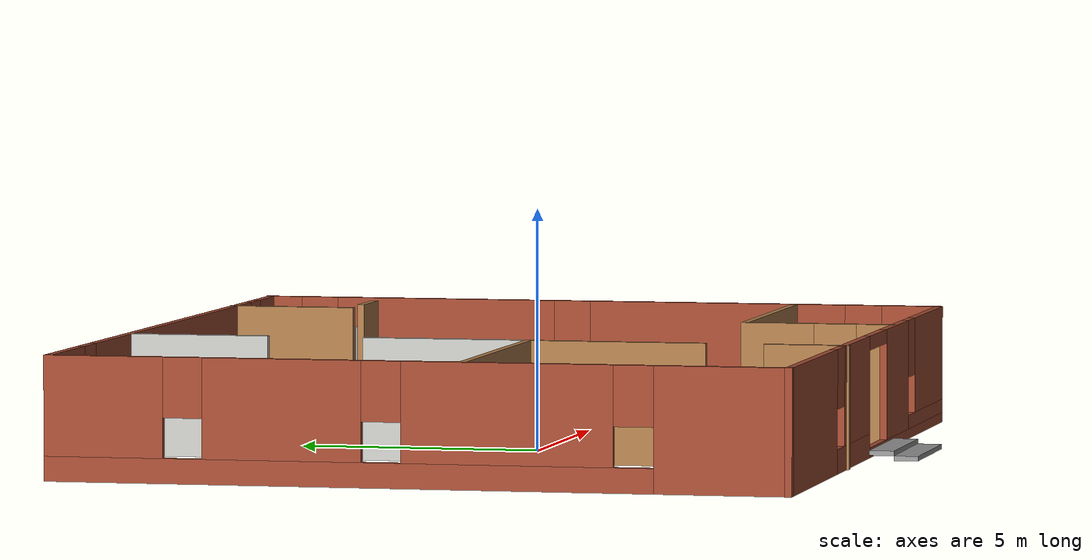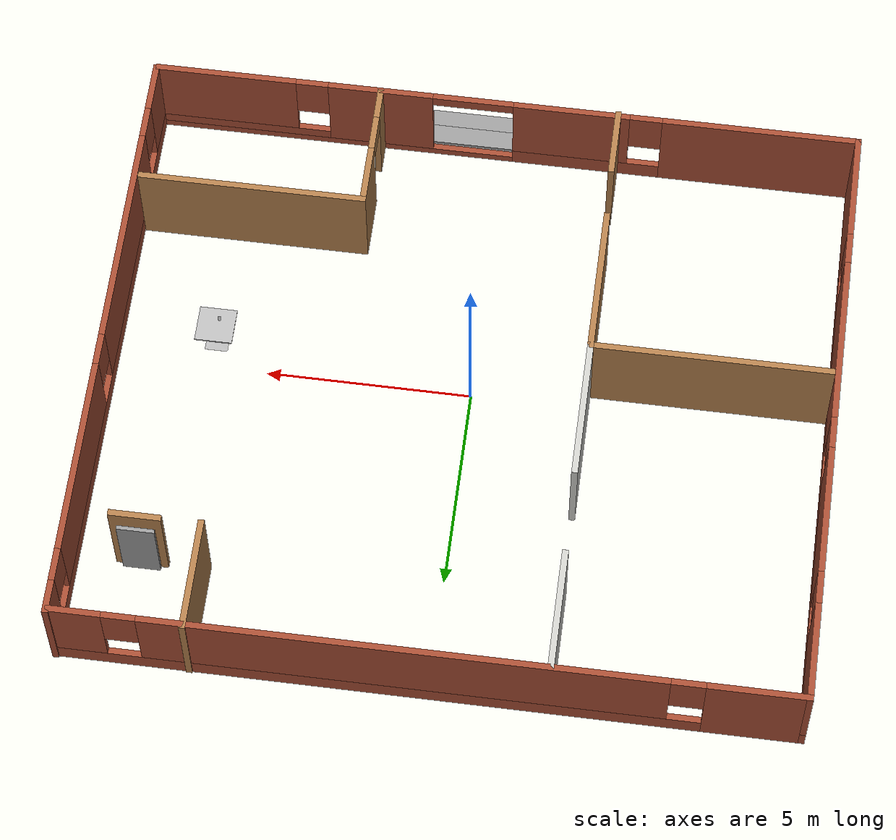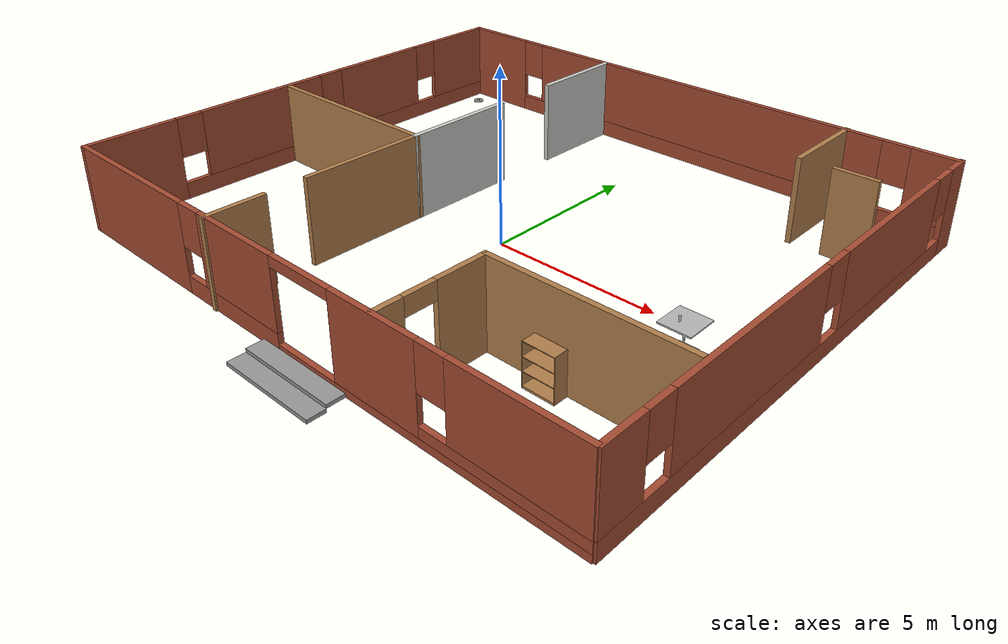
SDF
<?xml version='1.0'?>
<sdf version='1.6'>
  <model name='BuildingOne'>
    <link name='Door_2'>
      <pose frame=''>7.13008 5.46238 0 0 -0 0</pose>
      <self_collide>0</self_collide>
      <kinematic>0</kinematic>
      <visual name='Door_2_Visual'>
        <pose frame=''>0 0 1 0 -0 0</pose>
        <geometry>
          <box>
            <size>0.9 0.17 2</size>
          </box>
        </geometry>
        <material>
          <script>
            <uri>file://media/materials/scripts/gazebo.material</uri>
            <name>Gazebo/Grey</name>
          </script>
          <shader type='pixel'/>
          <ambient>0.3 0.3 0.3 1</ambient>
          <diffuse>0.7 0.7 0.7 1</diffuse>
          <specular>0.01 0.01 0.01 1</specular>
          <emissive>0 0 0 1</emissive>
        </material>
        <transparency>0</transparency>
        <cast_shadows>1</cast_shadows>
      </visual>
      <collision name='Door_2_Collision'>
        <laser_retro>0</laser_retro>
        <max_contacts>10</max_contacts>
        <pose frame=''>0 0 1 0 -0 0</pose>
        <geometry>
          <box>
            <size>0.9 0.17 2</size>
          </box>
        </geometry>
        <surface>
          <friction>
            <ode>
              <mu>1</mu>
              <mu2>1</mu2>
              <fdir1>0 0 0</fdir1>
              <slip1>0</slip1>
              <slip2>0</slip2>
            </ode>
            <torsional>
              <coefficient>1</coefficient>
              <patch_radius>0</patch_radius>
              <surface_radius>0</surface_radius>
              <use_patch_radius>1</use_patch_radius>
              <ode>
                <slip>0</slip>
              </ode>
            </torsional>
          </friction>
          <bounce>
            <restitution_coefficient>0</restitution_coefficient>
            <threshold>1e+06</threshold>
          </bounce>
          <contact>
            <collide_without_contact>0</collide_without_contact>
            <collide_without_contact_bitmask>1</collide_without_contact_bitmask>
            <collide_bitmask>1</collide_bitmask>
            <ode>
              <soft_cfm>0</soft_cfm>
              <soft_erp>0.2</soft_erp>
              <kp>1e+13</kp>
              <kd>1</kd>
              <max_vel>0.01</max_vel>
              <min_depth>0</min_depth>
            </ode>
            <bullet>
              <split_impulse>1</split_impulse>
              <split_impulse_penetration_threshold>-0.01</split_impulse_penetration_threshold>
              <soft_cfm>0</soft_cfm>
              <soft_erp>0.2</soft_erp>
              <kp>1e+13</kp>
              <kd>1</kd>
            </bullet>
          </contact>
        </surface>
      </collision>
    </link>
    <link name='Stairs_6'>
      <pose frame=''>0 0 0 0 -0 0</pose>
      <self_collide>0</self_collide>
      <kinematic>0</kinematic>
      <visual name='Stairs_6_Visual_0'>
        <pose frame=''>0.82349 -7.802 0.05 0 0 -3.14159</pose>
        <geometry>
          <box>
            <size>2.9 0.5 0.1</size>
          </box>
        </geometry>
        <material>
          <script>
            <uri>file://media/materials/scripts/gazebo.material</uri>
            <name>Gazebo/Grey</name>
          </script>
          <ambient>1 1 1 1</ambient>
          <shader type='pixel'/>
          <diffuse>0.7 0.7 0.7 1</diffuse>
          <specular>0.01 0.01 0.01 1</specular>
          <emissive>0 0 0 1</emissive>
        </material>
        <meta>
          <layer>0</layer>
        </meta>
        <transparency>0</transparency>
        <cast_shadows>1</cast_shadows>
      </visual>
      <visual name='Stairs_6_Visual_1'>
        <pose frame=''>0.82349 -7.302 0.15 0 0 -3.14159</pose>
        <geometry>
          <box>
            <size>2.9 0.5 0.1</size>
          </box>
        </geometry>
        <material>
          <script>
            <uri>file://media/materials/scripts/gazebo.material</uri>
            <name>Gazebo/Grey</name>
          </script>
          <ambient>1 1 1 1</ambient>
          <shader type='pixel'/>
          <diffuse>0.7 0.7 0.7 1</diffuse>
          <specular>0.01 0.01 0.01 1</specular>
          <emissive>0 0 0 1</emissive>
        </material>
        <meta>
          <layer>0</layer>
        </meta>
        <transparency>0</transparency>
        <cast_shadows>1</cast_shadows>
      </visual>
      <collision name='Stairs_6_Collision_0'>
        <laser_retro>0</laser_retro>
        <max_contacts>10</max_contacts>
        <pose frame=''>0.82349 -7.802 0.05 0 0 -3.14159</pose>
        <geometry>
          <box>
            <size>2.9 0.5 0.1</size>
          </box>
        </geometry>
        <surface>
          <friction>
            <ode>
              <mu>1</mu>
              <mu2>1</mu2>
              <fdir1>0 0 0</fdir1>
              <slip1>0</slip1>
              <slip2>0</slip2>
            </ode>
            <torsional>
              <coefficient>1</coefficient>
              <patch_radius>0</patch_radius>
              <surface_radius>0</surface_radius>
              <use_patch_radius>1</use_patch_radius>
              <ode>
                <slip>0</slip>
              </ode>
            </torsional>
          </friction>
          <bounce>
            <restitution_coefficient>0</restitution_coefficient>
            <threshold>1e+06</threshold>
          </bounce>
          <contact>
            <collide_without_contact>0</collide_without_contact>
            <collide_without_contact_bitmask>1</collide_without_contact_bitmask>
            <collide_bitmask>1</collide_bitmask>
            <ode>
              <soft_cfm>0</soft_cfm>
              <soft_erp>0.2</soft_erp>
              <kp>1e+13</kp>
              <kd>1</kd>
              <max_vel>0.01</max_vel>
              <min_depth>0</min_depth>
            </ode>
            <bullet>
              <split_impulse>1</split_impulse>
              <split_impulse_penetration_threshold>-0.01</split_impulse_penetration_threshold>
              <soft_cfm>0</soft_cfm>
              <soft_erp>0.2</soft_erp>
              <kp>1e+13</kp>
              <kd>1</kd>
            </bullet>
          </contact>
        </surface>
      </collision>
      <collision name='Stairs_6_Collision_1'>
        <laser_retro>0</laser_retro>
        <max_contacts>10</max_contacts>
        <pose frame=''>0.82349 -7.302 0.15 0 0 -3.14159</pose>
        <geometry>
          <box>
            <size>2.9 0.5 0.1</size>
          </box>
        </geometry>
        <surface>
          <friction>
            <ode>
              <mu>1</mu>
              <mu2>1</mu2>
              <fdir1>0 0 0</fdir1>
              <slip1>0</slip1>
              <slip2>0</slip2>
            </ode>
            <torsional>
              <coefficient>1</coefficient>
              <patch_radius>0</patch_radius>
              <surface_radius>0</surface_radius>
              <use_patch_radius>1</use_patch_radius>
              <ode>
                <slip>0</slip>
              </ode>
            </torsional>
          </friction>
          <bounce>
            <restitution_coefficient>0</restitution_coefficient>
            <threshold>1e+06</threshold>
          </bounce>
          <contact>
            <collide_without_contact>0</collide_without_contact>
            <collide_without_contact_bitmask>1</collide_without_contact_bitmask>
            <collide_bitmask>1</collide_bitmask>
            <ode>
              <soft_cfm>0</soft_cfm>
              <soft_erp>0.2</soft_erp>
              <kp>1e+13</kp>
              <kd>1</kd>
              <max_vel>0.01</max_vel>
              <min_depth>0</min_depth>
            </ode>
            <bullet>
              <split_impulse>1</split_impulse>
              <split_impulse_penetration_threshold>-0.01</split_impulse_penetration_threshold>
              <soft_cfm>0</soft_cfm>
              <soft_erp>0.2</soft_erp>
              <kp>1e+13</kp>
              <kd>1</kd>
            </bullet>
          </contact>
        </surface>
      </collision>
    </link>
    <link name='Wall_0'>
      <pose frame=''>-8.67851 0.522825 0 0 -0 1.5708</pose>
      <self_collide>0</self_collide>
      <kinematic>0</kinematic>
      <visual name='Wall_0_Visual_0'>
        <pose frame=''>-6.13494 0 1.25 0 -0 0</pose>
        <geometry>
          <box>
            <size>2.73012 0.15 2.5</size>
          </box>
        </geometry>
        <material>
          <script>
            <uri>file://media/materials/scripts/gazebo.material</uri>
            <name>Gazebo/Bricks</name>
          </script>
          <ambient>1 1 1 1</ambient>
          <shader type='pixel'/>
          <diffuse>1 1 1 1</diffuse>
          <specular>0.2 0.2 0.2 1</specular>
          <emissive>0 0 0 1</emissive>
        </material>
        <meta>
          <layer>0</layer>
        </meta>
        <transparency>0</transparency>
        <cast_shadows>1</cast_shadows>
      </visual>
      <visual name='Wall_0_Visual_1'>
        <pose frame=''>1.36506 0 0.25 0 -0 0</pose>
        <geometry>
          <box>
            <size>12.2699 0.15 0.5</size>
          </box>
        </geometry>
        <material>
          <script>
            <uri>file://media/materials/scripts/gazebo.material</uri>
            <name>Gazebo/Bricks</name>
          </script>
          <ambient>1 1 1 1</ambient>
          <shader type='pixel'/>
          <diffuse>1 1 1 1</diffuse>
          <specular>0.2 0.2 0.2 1</specular>
          <emissive>0 0 0 1</emissive>
        </material>
        <meta>
          <layer>0</layer>
        </meta>
        <transparency>0</transparency>
        <cast_shadows>1</cast_shadows>
      </visual>
      <visual name='Wall_0_Visual_2'>
        <pose frame=''>-1.85526 0 1.5 0 -0 0</pose>
        <geometry>
          <box>
            <size>4.22924 0.15 2</size>
          </box>
        </geometry>
        <material>
          <script>
            <uri>file://media/materials/scripts/gazebo.material</uri>
            <name>Gazebo/Bricks</name>
          </script>
          <ambient>1 1 1 1</ambient>
          <shader type='pixel'/>
          <diffuse>1 1 1 1</diffuse>
          <specular>0.2 0.2 0.2 1</specular>
          <emissive>0 0 0 1</emissive>
        </material>
        <meta>
          <layer>0</layer>
        </meta>
        <transparency>0</transparency>
        <cast_shadows>1</cast_shadows>
      </visual>
      <visual name='Wall_0_Visual_3'>
        <pose frame=''>2.6657 0 1.5 0 -0 0</pose>
        <geometry>
          <box>
            <size>3.21269 0.15 2</size>
          </box>
        </geometry>
        <material>
          <script>
            <uri>file://media/materials/scripts/gazebo.material</uri>
            <name>Gazebo/Bricks</name>
          </script>
          <ambient>1 1 1 1</ambient>
          <shader type='pixel'/>
          <diffuse>1 1 1 1</diffuse>
          <specular>0.2 0.2 0.2 1</specular>
          <emissive>0 0 0 1</emissive>
        </material>
        <meta>
          <layer>0</layer>
        </meta>
        <transparency>0</transparency>
        <cast_shadows>1</cast_shadows>
      </visual>
      <visual name='Wall_0_Visual_4'>
        <pose frame=''>6.28602 0 1.5 0 -0 0</pose>
        <geometry>
          <box>
            <size>2.42796 0.15 2</size>
          </box>
        </geometry>
        <material>
          <script>
            <uri>file://media/materials/scripts/gazebo.material</uri>
            <name>Gazebo/Bricks</name>
          </script>
          <ambient>1 1 1 1</ambient>
          <shader type='pixel'/>
          <diffuse>1 1 1 1</diffuse>
          <specular>0.2 0.2 0.2 1</specular>
          <emissive>0 0 0 1</emissive>
        </material>
        <meta>
          <layer>0</layer>
        </meta>
        <transparency>0</transparency>
        <cast_shadows>1</cast_shadows>
      </visual>
      <visual name='Wall_0_Visual_5'>
        <pose frame=''>-4.36988 0 1.9 0 -0 0</pose>
        <geometry>
          <box>
            <size>0.8 0.15 1.2</size>
          </box>
        </geometry>
        <material>
          <script>
            <uri>file://media/materials/scripts/gazebo.material</uri>
            <name>Gazebo/Bricks</name>
          </script>
          <ambient>1 1 1 1</ambient>
          <shader type='pixel'/>
          <diffuse>1 1 1 1</diffuse>
          <specular>0.2 0.2 0.2 1</specular>
          <emissive>0 0 0 1</emissive>
        </material>
        <meta>
          <layer>0</layer>
        </meta>
        <transparency>0</transparency>
        <cast_shadows>1</cast_shadows>
      </visual>
      <visual name='Wall_0_Visual_6'>
        <pose frame=''>0.659356 0 1.9 0 -0 0</pose>
        <geometry>
          <box>
            <size>0.8 0.15 1.2</size>
          </box>
        </geometry>
        <material>
          <script>
            <uri>file://media/materials/scripts/gazebo.material</uri>
            <name>Gazebo/Bricks</name>
          </script>
          <ambient>1 1 1 1</ambient>
          <shader type='pixel'/>
          <diffuse>1 1 1 1</diffuse>
          <specular>0.2 0.2 0.2 1</specular>
          <emissive>0 0 0 1</emissive>
        </material>
        <meta>
          <layer>0</layer>
        </meta>
        <transparency>0</transparency>
        <cast_shadows>1</cast_shadows>
      </visual>
      <visual name='Wall_0_Visual_7'>
        <pose frame=''>4.67204 0 1.9 0 -0 0</pose>
        <geometry>
          <box>
            <size>0.8 0.15 1.2</size>
          </box>
        </geometry>
        <material>
          <script>
            <uri>file://media/materials/scripts/gazebo.material</uri>
            <name>Gazebo/Bricks</name>
          </script>
          <ambient>1 1 1 1</ambient>
          <shader type='pixel'/>
          <diffuse>1 1 1 1</diffuse>
          <specular>0.2 0.2 0.2 1</specular>
          <emissive>0 0 0 1</emissive>
        </material>
        <meta>
          <layer>0</layer>
        </meta>
        <transparency>0</transparency>
        <cast_shadows>1</cast_shadows>
      </visual>
      <collision name='Wall_0_Collision_0'>
        <laser_retro>0</laser_retro>
        <max_contacts>10</max_contacts>
        <pose frame=''>-6.13494 0 1.25 0 -0 0</pose>
        <geometry>
          <box>
            <size>2.73012 0.15 2.5</size>
          </box>
        </geometry>
        <surface>
          <friction>
            <ode>
              <mu>1</mu>
              <mu2>1</mu2>
              <fdir1>0 0 0</fdir1>
              <slip1>0</slip1>
              <slip2>0</slip2>
            </ode>
            <torsional>
              <coefficient>1</coefficient>
              <patch_radius>0</patch_radius>
              <surface_radius>0</surface_radius>
              <use_patch_radius>1</use_patch_radius>
              <ode>
                <slip>0</slip>
              </ode>
            </torsional>
          </friction>
          <bounce>
            <restitution_coefficient>0</restitution_coefficient>
            <threshold>1e+06</threshold>
          </bounce>
          <contact>
            <collide_without_contact>0</collide_without_contact>
            <collide_without_contact_bitmask>1</collide_without_contact_bitmask>
            <collide_bitmask>1</collide_bitmask>
            <ode>
              <soft_cfm>0</soft_cfm>
              <soft_erp>0.2</soft_erp>
              <kp>1e+13</kp>
              <kd>1</kd>
              <max_vel>0.01</max_vel>
              <min_depth>0</min_depth>
            </ode>
            <bullet>
              <split_impulse>1</split_impulse>
              <split_impulse_penetration_threshold>-0.01</split_impulse_penetration_threshold>
              <soft_cfm>0</soft_cfm>
              <soft_erp>0.2</soft_erp>
              <kp>1e+13</kp>
              <kd>1</kd>
            </bullet>
          </contact>
        </surface>
      </collision>
      <collision name='Wall_0_Collision_2'>
        <laser_retro>0</laser_retro>
        <max_contacts>10</max_contacts>
        <pose frame=''>-1.85526 0 1.5 0 -0 0</pose>
        <geometry>
          <box>
            <size>4.22924 0.15 2</size>
          </box>
        </geometry>
        <surface>
          <friction>
            <ode>
              <mu>1</mu>
              <mu2>1</mu2>
              <fdir1>0 0 0</fdir1>
              <slip1>0</slip1>
              <slip2>0</slip2>
            </ode>
            <torsional>
              <coefficient>1</coefficient>
              <patch_radius>0</patch_radius>
              <surface_radius>0</surface_radius>
              <use_patch_radius>1</use_patch_radius>
              <ode>
                <slip>0</slip>
              </ode>
            </torsional>
          </friction>
          <bounce>
            <restitution_coefficient>0</restitution_coefficient>
            <threshold>1e+06</threshold>
          </bounce>
          <contact>
            <collide_without_contact>0</collide_without_contact>
            <collide_without_contact_bitmask>1</collide_without_contact_bitmask>
            <collide_bitmask>1</collide_bitmask>
            <ode>
              <soft_cfm>0</soft_cfm>
              <soft_erp>0.2</soft_erp>
              <kp>1e+13</kp>
              <kd>1</kd>
              <max_vel>0.01</max_vel>
              <min_depth>0</min_depth>
            </ode>
            <bullet>
              <split_impulse>1</split_impulse>
              <split_impulse_penetration_threshold>-0.01</split_impulse_penetration_threshold>
              <soft_cfm>0</soft_cfm>
              <soft_erp>0.2</soft_erp>
              <kp>1e+13</kp>
              <kd>1</kd>
            </bullet>
          </contact>
        </surface>
      </collision>
      <collision name='Wall_0_Collision_1'>
        <laser_retro>0</laser_retro>
        <max_contacts>10</max_contacts>
        <pose frame=''>1.36506 0 0.25 0 -0 0</pose>
        <geometry>
          <box>
            <size>12.2699 0.15 0.5</size>
          </box>
        </geometry>
        <surface>
          <friction>
            <ode>
              <mu>1</mu>
              <mu2>1</mu2>
              <fdir1>0 0 0</fdir1>
              <slip1>0</slip1>
              <slip2>0</slip2>
            </ode>
            <torsional>
              <coefficient>1</coefficient>
              <patch_radius>0</patch_radius>
              <surface_radius>0</surface_radius>
              <use_patch_radius>1</use_patch_radius>
              <ode>
                <slip>0</slip>
              </ode>
            </torsional>
          </friction>
          <bounce>
            <restitution_coefficient>0</restitution_coefficient>
            <threshold>1e+06</threshold>
          </bounce>
          <contact>
            <collide_without_contact>0</collide_without_contact>
            <collide_without_contact_bitmask>1</collide_without_contact_bitmask>
            <collide_bitmask>1</collide_bitmask>
            <ode>
              <soft_cfm>0</soft_cfm>
              <soft_erp>0.2</soft_erp>
              <kp>1e+13</kp>
              <kd>1</kd>
              <max_vel>0.01</max_vel>
              <min_depth>0</min_depth>
            </ode>
            <bullet>
              <split_impulse>1</split_impulse>
              <split_impulse_penetration_threshold>-0.01</split_impulse_penetration_threshold>
              <soft_cfm>0</soft_cfm>
              <soft_erp>0.2</soft_erp>
              <kp>1e+13</kp>
              <kd>1</kd>
            </bullet>
          </contact>
        </surface>
      </collision>
      <collision name='Wall_0_Collision_4'>
        <laser_retro>0</laser_retro>
        <max_contacts>10</max_contacts>
        <pose frame=''>6.28602 0 1.5 0 -0 0</pose>
        <geometry>
          <box>
            <size>2.42796 0.15 2</size>
          </box>
        </geometry>
        <surface>
          <friction>
            <ode>
              <mu>1</mu>
              <mu2>1</mu2>
              <fdir1>0 0 0</fdir1>
              <slip1>0</slip1>
              <slip2>0</slip2>
            </ode>
            <torsional>
              <coefficient>1</coefficient>
              <patch_radius>0</patch_radius>
              <surface_radius>0</surface_radius>
              <use_patch_radius>1</use_patch_radius>
              <ode>
                <slip>0</slip>
              </ode>
            </torsional>
          </friction>
          <bounce>
            <restitution_coefficient>0</restitution_coefficient>
            <threshold>1e+06</threshold>
          </bounce>
          <contact>
            <collide_without_contact>0</collide_without_contact>
            <collide_without_contact_bitmask>1</collide_without_contact_bitmask>
            <collide_bitmask>1</collide_bitmask>
            <ode>
              <soft_cfm>0</soft_cfm>
              <soft_erp>0.2</soft_erp>
              <kp>1e+13</kp>
              <kd>1</kd>
              <max_vel>0.01</max_vel>
              <min_depth>0</min_depth>
            </ode>
            <bullet>
              <split_impulse>1</split_impulse>
              <split_impulse_penetration_threshold>-0.01</split_impulse_penetration_threshold>
              <soft_cfm>0</soft_cfm>
              <soft_erp>0.2</soft_erp>
              <kp>1e+13</kp>
              <kd>1</kd>
            </bullet>
          </contact>
        </surface>
      </collision>
      <collision name='Wall_0_Collision_3'>
        <laser_retro>0</laser_retro>
        <max_contacts>10</max_contacts>
        <pose frame=''>2.6657 0 1.5 0 -0 0</pose>
        <geometry>
          <box>
            <size>3.21269 0.15 2</size>
          </box>
        </geometry>
        <surface>
          <friction>
            <ode>
              <mu>1</mu>
              <mu2>1</mu2>
              <fdir1>0 0 0</fdir1>
              <slip1>0</slip1>
              <slip2>0</slip2>
            </ode>
            <torsional>
              <coefficient>1</coefficient>
              <patch_radius>0</patch_radius>
              <surface_radius>0</surface_radius>
              <use_patch_radius>1</use_patch_radius>
              <ode>
                <slip>0</slip>
              </ode>
            </torsional>
          </friction>
          <bounce>
            <restitution_coefficient>0</restitution_coefficient>
            <threshold>1e+06</threshold>
          </bounce>
          <contact>
            <collide_without_contact>0</collide_without_contact>
            <collide_without_contact_bitmask>1</collide_without_contact_bitmask>
            <collide_bitmask>1</collide_bitmask>
            <ode>
              <soft_cfm>0</soft_cfm>
              <soft_erp>0.2</soft_erp>
              <kp>1e+13</kp>
              <kd>1</kd>
              <max_vel>0.01</max_vel>
              <min_depth>0</min_depth>
            </ode>
            <bullet>
              <split_impulse>1</split_impulse>
              <split_impulse_penetration_threshold>-0.01</split_impulse_penetration_threshold>
              <soft_cfm>0</soft_cfm>
              <soft_erp>0.2</soft_erp>
              <kp>1e+13</kp>
              <kd>1</kd>
            </bullet>
          </contact>
        </surface>
      </collision>
      <collision name='Wall_0_Collision_5'>
        <laser_retro>0</laser_retro>
        <max_contacts>10</max_contacts>
        <pose frame=''>-4.36988 0 1.9 0 -0 0</pose>
        <geometry>
          <box>
            <size>0.8 0.15 1.2</size>
          </box>
        </geometry>
        <surface>
          <friction>
            <ode>
              <mu>1</mu>
              <mu2>1</mu2>
              <fdir1>0 0 0</fdir1>
              <slip1>0</slip1>
              <slip2>0</slip2>
            </ode>
            <torsional>
              <coefficient>1</coefficient>
              <patch_radius>0</patch_radius>
              <surface_radius>0</surface_radius>
              <use_patch_radius>1</use_patch_radius>
              <ode>
                <slip>0</slip>
              </ode>
            </torsional>
          </friction>
          <bounce>
            <restitution_coefficient>0</restitution_coefficient>
            <threshold>1e+06</threshold>
          </bounce>
          <contact>
            <collide_without_contact>0</collide_without_contact>
            <collide_without_contact_bitmask>1</collide_without_contact_bitmask>
            <collide_bitmask>1</collide_bitmask>
            <ode>
              <soft_cfm>0</soft_cfm>
              <soft_erp>0.2</soft_erp>
              <kp>1e+13</kp>
              <kd>1</kd>
              <max_vel>0.01</max_vel>
              <min_depth>0</min_depth>
            </ode>
            <bullet>
              <split_impulse>1</split_impulse>
              <split_impulse_penetration_threshold>-0.01</split_impulse_penetration_threshold>
              <soft_cfm>0</soft_cfm>
              <soft_erp>0.2</soft_erp>
              <kp>1e+13</kp>
              <kd>1</kd>
            </bullet>
          </contact>
        </surface>
      </collision>
      <collision name='Wall_0_Collision_7'>
        <laser_retro>0</laser_retro>
        <max_contacts>10</max_contacts>
        <pose frame=''>4.67204 0 1.9 0 -0 0</pose>
        <geometry>
          <box>
            <size>0.8 0.15 1.2</size>
          </box>
        </geometry>
        <surface>
          <friction>
            <ode>
              <mu>1</mu>
              <mu2>1</mu2>
              <fdir1>0 0 0</fdir1>
              <slip1>0</slip1>
              <slip2>0</slip2>
            </ode>
            <torsional>
              <coefficient>1</coefficient>
              <patch_radius>0</patch_radius>
              <surface_radius>0</surface_radius>
              <use_patch_radius>1</use_patch_radius>
              <ode>
                <slip>0</slip>
              </ode>
            </torsional>
          </friction>
          <bounce>
            <restitution_coefficient>0</restitution_coefficient>
            <threshold>1e+06</threshold>
          </bounce>
          <contact>
            <collide_without_contact>0</collide_without_contact>
            <collide_without_contact_bitmask>1</collide_without_contact_bitmask>
            <collide_bitmask>1</collide_bitmask>
            <ode>
              <soft_cfm>0</soft_cfm>
              <soft_erp>0.2</soft_erp>
              <kp>1e+13</kp>
              <kd>1</kd>
              <max_vel>0.01</max_vel>
              <min_depth>0</min_depth>
            </ode>
            <bullet>
              <split_impulse>1</split_impulse>
              <split_impulse_penetration_threshold>-0.01</split_impulse_penetration_threshold>
              <soft_cfm>0</soft_cfm>
              <soft_erp>0.2</soft_erp>
              <kp>1e+13</kp>
              <kd>1</kd>
            </bullet>
          </contact>
        </surface>
      </collision>
      <collision name='Wall_0_Collision_6'>
        <laser_retro>0</laser_retro>
        <max_contacts>10</max_contacts>
        <pose frame=''>0.659356 0 1.9 0 -0 0</pose>
        <geometry>
          <box>
            <size>0.8 0.15 1.2</size>
          </box>
        </geometry>
        <surface>
          <friction>
            <ode>
              <mu>1</mu>
              <mu2>1</mu2>
              <fdir1>0 0 0</fdir1>
              <slip1>0</slip1>
              <slip2>0</slip2>
            </ode>
            <torsional>
              <coefficient>1</coefficient>
              <patch_radius>0</patch_radius>
              <surface_radius>0</surface_radius>
              <use_patch_radius>1</use_patch_radius>
              <ode>
                <slip>0</slip>
              </ode>
            </torsional>
          </friction>
          <bounce>
            <restitution_coefficient>0</restitution_coefficient>
            <threshold>1e+06</threshold>
          </bounce>
          <contact>
            <collide_without_contact>0</collide_without_contact>
            <collide_without_contact_bitmask>1</collide_without_contact_bitmask>
            <collide_bitmask>1</collide_bitmask>
            <ode>
              <soft_cfm>0</soft_cfm>
              <soft_erp>0.2</soft_erp>
              <kp>1e+13</kp>
              <kd>1</kd>
              <max_vel>0.01</max_vel>
              <min_depth>0</min_depth>
            </ode>
            <bullet>
              <split_impulse>1</split_impulse>
              <split_impulse_penetration_threshold>-0.01</split_impulse_penetration_threshold>
              <soft_cfm>0</soft_cfm>
              <soft_erp>0.2</soft_erp>
              <kp>1e+13</kp>
              <kd>1</kd>
            </bullet>
          </contact>
        </surface>
      </collision>
    </link>
    <link name='Wall_11'>
      <pose frame=''>3.11744 -5.29319 0 0 -0 1.57077</pose>
      <self_collide>0</self_collide>
      <kinematic>0</kinematic>
      <visual name='Wall_11_Visual_0'>
        <pose frame=''>-1.22398 0 1.25 0 -0 0</pose>
        <geometry>
          <box>
            <size>0.802043 0.15 2.5</size>
          </box>
        </geometry>
        <material>
          <script>
            <uri>file://media/materials/scripts/gazebo.material</uri>
            <name>Gazebo/Wood</name>
          </script>
          <ambient>1 1 1 1</ambient>
          <shader type='pixel'/>
          <diffuse>1 1 1 1</diffuse>
          <specular>0.2 0.2 0.2 1</specular>
          <emissive>0 0 0 1</emissive>
        </material>
        <meta>
          <layer>0</layer>
        </meta>
        <transparency>0</transparency>
        <cast_shadows>1</cast_shadows>
      </visual>
      <visual name='Wall_11_Visual_1'>
        <pose frame=''>0.851022 0 1.25 0 -0 0</pose>
        <geometry>
          <box>
            <size>1.54796 0.15 2.5</size>
          </box>
        </geometry>
        <material>
          <script>
            <uri>file://media/materials/scripts/gazebo.material</uri>
            <name>Gazebo/Wood</name>
          </script>
          <ambient>1 1 1 1</ambient>
          <shader type='pixel'/>
          <diffuse>1 1 1 1</diffuse>
          <specular>0.2 0.2 0.2 1</specular>
          <emissive>0 0 0 1</emissive>
        </material>
        <meta>
          <layer>0</layer>
        </meta>
        <transparency>0</transparency>
        <cast_shadows>1</cast_shadows>
      </visual>
      <visual name='Wall_11_Visual_2'>
        <pose frame=''>-0.372957 0 2.25 0 -0 0</pose>
        <geometry>
          <box>
            <size>0.9 0.15 0.5</size>
          </box>
        </geometry>
        <material>
          <script>
            <uri>file://media/materials/scripts/gazebo.material</uri>
            <name>Gazebo/Wood</name>
          </script>
          <ambient>1 1 1 1</ambient>
          <shader type='pixel'/>
          <diffuse>1 1 1 1</diffuse>
          <specular>0.2 0.2 0.2 1</specular>
          <emissive>0 0 0 1</emissive>
        </material>
        <meta>
          <layer>0</layer>
        </meta>
        <transparency>0</transparency>
        <cast_shadows>1</cast_shadows>
      </visual>
      <collision name='Wall_11_Collision_0'>
        <laser_retro>0</laser_retro>
        <max_contacts>10</max_contacts>
        <pose frame=''>-1.22398 0 1.25 0 -0 0</pose>
        <geometry>
          <box>
            <size>0.802043 0.15 2.5</size>
          </box>
        </geometry>
        <surface>
          <friction>
            <ode>
              <mu>1</mu>
              <mu2>1</mu2>
              <fdir1>0 0 0</fdir1>
              <slip1>0</slip1>
              <slip2>0</slip2>
            </ode>
            <torsional>
              <coefficient>1</coefficient>
              <patch_radius>0</patch_radius>
              <surface_radius>0</surface_radius>
              <use_patch_radius>1</use_patch_radius>
              <ode>
                <slip>0</slip>
              </ode>
            </torsional>
          </friction>
          <bounce>
            <restitution_coefficient>0</restitution_coefficient>
            <threshold>1e+06</threshold>
          </bounce>
          <contact>
            <collide_without_contact>0</collide_without_contact>
            <collide_without_contact_bitmask>1</collide_without_contact_bitmask>
            <collide_bitmask>1</collide_bitmask>
            <ode>
              <soft_cfm>0</soft_cfm>
              <soft_erp>0.2</soft_erp>
              <kp>1e+13</kp>
              <kd>1</kd>
              <max_vel>0.01</max_vel>
              <min_depth>0</min_depth>
            </ode>
            <bullet>
              <split_impulse>1</split_impulse>
              <split_impulse_penetration_threshold>-0.01</split_impulse_penetration_threshold>
              <soft_cfm>0</soft_cfm>
              <soft_erp>0.2</soft_erp>
              <kp>1e+13</kp>
              <kd>1</kd>
            </bullet>
          </contact>
        </surface>
      </collision>
      <collision name='Wall_11_Collision_1'>
        <laser_retro>0</laser_retro>
        <max_contacts>10</max_contacts>
        <pose frame=''>0.851022 0 1.25 0 -0 0</pose>
        <geometry>
          <box>
            <size>1.54796 0.15 2.5</size>
          </box>
        </geometry>
        <surface>
          <friction>
            <ode>
              <mu>1</mu>
              <mu2>1</mu2>
              <fdir1>0 0 0</fdir1>
              <slip1>0</slip1>
              <slip2>0</slip2>
            </ode>
            <torsional>
              <coefficient>1</coefficient>
              <patch_radius>0</patch_radius>
              <surface_radius>0</surface_radius>
              <use_patch_radius>1</use_patch_radius>
              <ode>
                <slip>0</slip>
              </ode>
            </torsional>
          </friction>
          <bounce>
            <restitution_coefficient>0</restitution_coefficient>
            <threshold>1e+06</threshold>
          </bounce>
          <contact>
            <collide_without_contact>0</collide_without_contact>
            <collide_without_contact_bitmask>1</collide_without_contact_bitmask>
            <collide_bitmask>1</collide_bitmask>
            <ode>
              <soft_cfm>0</soft_cfm>
              <soft_erp>0.2</soft_erp>
              <kp>1e+13</kp>
              <kd>1</kd>
              <max_vel>0.01</max_vel>
              <min_depth>0</min_depth>
            </ode>
            <bullet>
              <split_impulse>1</split_impulse>
              <split_impulse_penetration_threshold>-0.01</split_impulse_penetration_threshold>
              <soft_cfm>0</soft_cfm>
              <soft_erp>0.2</soft_erp>
              <kp>1e+13</kp>
              <kd>1</kd>
            </bullet>
          </contact>
        </surface>
      </collision>
      <collision name='Wall_11_Collision_2'>
        <laser_retro>0</laser_retro>
        <max_contacts>10</max_contacts>
        <pose frame=''>-0.372957 0 2.25 0 -0 0</pose>
        <geometry>
          <box>
            <size>0.9 0.15 0.5</size>
          </box>
        </geometry>
        <surface>
          <friction>
            <ode>
              <mu>1</mu>
              <mu2>1</mu2>
              <fdir1>0 0 0</fdir1>
              <slip1>0</slip1>
              <slip2>0</slip2>
            </ode>
            <torsional>
              <coefficient>1</coefficient>
              <patch_radius>0</patch_radius>
              <surface_radius>0</surface_radius>
              <use_patch_radius>1</use_patch_radius>
              <ode>
                <slip>0</slip>
              </ode>
            </torsional>
          </friction>
          <bounce>
            <restitution_coefficient>0</restitution_coefficient>
            <threshold>1e+06</threshold>
          </bounce>
          <contact>
            <collide_without_contact>0</collide_without_contact>
            <collide_without_contact_bitmask>1</collide_without_contact_bitmask>
            <collide_bitmask>1</collide_bitmask>
            <ode>
              <soft_cfm>0</soft_cfm>
              <soft_erp>0.2</soft_erp>
              <kp>1e+13</kp>
              <kd>1</kd>
              <max_vel>0.01</max_vel>
              <min_depth>0</min_depth>
            </ode>
            <bullet>
              <split_impulse>1</split_impulse>
              <split_impulse_penetration_threshold>-0.01</split_impulse_penetration_threshold>
              <soft_cfm>0</soft_cfm>
              <soft_erp>0.2</soft_erp>
              <kp>1e+13</kp>
              <kd>1</kd>
            </bullet>
          </contact>
        </surface>
      </collision>
    </link>
    <link name='Wall_12'>
      <pose frame=''>5.84249 -3.74317 0 0 -0 0</pose>
      <self_collide>0</self_collide>
      <kinematic>0</kinematic>
      <visual name='Wall_12_Visual'>
        <pose frame=''>0 0 1.25 0 -0 0</pose>
        <geometry>
          <box>
            <size>5.6 0.15 2.5</size>
          </box>
        </geometry>
        <material>
          <script>
            <uri>file://media/materials/scripts/gazebo.material</uri>
            <name>Gazebo/Wood</name>
          </script>
          <ambient>1 1 1 1</ambient>
          <shader type='pixel'/>
          <diffuse>1 1 1 1</diffuse>
          <specular>0.2 0.2 0.2 1</specular>
          <emissive>0 0 0 1</emissive>
        </material>
        <meta>
          <layer>0</layer>
        </meta>
        <transparency>0</transparency>
        <cast_shadows>1</cast_shadows>
      </visual>
      <collision name='Wall_12_Collision'>
        <laser_retro>0</laser_retro>
        <max_contacts>10</max_contacts>
        <pose frame=''>0 0 1.25 0 -0 0</pose>
        <geometry>
          <box>
            <size>5.6 0.15 2.5</size>
          </box>
        </geometry>
        <surface>
          <friction>
            <ode>
              <mu>1</mu>
              <mu2>1</mu2>
              <fdir1>0 0 0</fdir1>
              <slip1>0</slip1>
              <slip2>0</slip2>
            </ode>
            <torsional>
              <coefficient>1</coefficient>
              <patch_radius>0</patch_radius>
              <surface_radius>0</surface_radius>
              <use_patch_radius>1</use_patch_radius>
              <ode>
                <slip>0</slip>
              </ode>
            </torsional>
          </friction>
          <bounce>
            <restitution_coefficient>0</restitution_coefficient>
            <threshold>1e+06</threshold>
          </bounce>
          <contact>
            <collide_without_contact>0</collide_without_contact>
            <collide_without_contact_bitmask>1</collide_without_contact_bitmask>
            <collide_bitmask>1</collide_bitmask>
            <ode>
              <soft_cfm>0</soft_cfm>
              <soft_erp>0.2</soft_erp>
              <kp>1e+13</kp>
              <kd>1</kd>
              <max_vel>0.01</max_vel>
              <min_depth>0</min_depth>
            </ode>
            <bullet>
              <split_impulse>1</split_impulse>
              <split_impulse_penetration_threshold>-0.01</split_impulse_penetration_threshold>
              <soft_cfm>0</soft_cfm>
              <soft_erp>0.2</soft_erp>
              <kp>1e+13</kp>
              <kd>1</kd>
            </bullet>
          </contact>
        </surface>
      </collision>
    </link>
    <link name='Wall_15'>
      <pose frame=''>-5.72816 -0.422895 0 0 -0 0</pose>
      <self_collide>0</self_collide>
      <kinematic>0</kinematic>
      <visual name='Wall_15_Visual'>
        <pose frame=''>0 0 1.25 0 -0 0</pose>
        <geometry>
          <box>
            <size>6 0.15 2.5</size>
          </box>
        </geometry>
        <material>
          <script>
            <uri>file://media/materials/scripts/gazebo.material</uri>
            <name>Gazebo/Wood</name>
          </script>
          <ambient>1 1 1 1</ambient>
          <shader type='pixel'/>
          <diffuse>1 1 1 1</diffuse>
          <specular>0.2 0.2 0.2 1</specular>
          <emissive>0 0 0 1</emissive>
        </material>
        <meta>
          <layer>0</layer>
        </meta>
        <transparency>0</transparency>
        <cast_shadows>1</cast_shadows>
      </visual>
      <collision name='Wall_15_Collision'>
        <laser_retro>0</laser_retro>
        <max_contacts>10</max_contacts>
        <pose frame=''>0 0 1.25 0 -0 0</pose>
        <geometry>
          <box>
            <size>6 0.15 2.5</size>
          </box>
        </geometry>
        <surface>
          <friction>
            <ode>
              <mu>1</mu>
              <mu2>1</mu2>
              <fdir1>0 0 0</fdir1>
              <slip1>0</slip1>
              <slip2>0</slip2>
            </ode>
            <torsional>
              <coefficient>1</coefficient>
              <patch_radius>0</patch_radius>
              <surface_radius>0</surface_radius>
              <use_patch_radius>1</use_patch_radius>
              <ode>
                <slip>0</slip>
              </ode>
            </torsional>
          </friction>
          <bounce>
            <restitution_coefficient>0</restitution_coefficient>
            <threshold>1e+06</threshold>
          </bounce>
          <contact>
            <collide_without_contact>0</collide_without_contact>
            <collide_without_contact_bitmask>1</collide_without_contact_bitmask>
            <collide_bitmask>1</collide_bitmask>
            <ode>
              <soft_cfm>0</soft_cfm>
              <soft_erp>0.2</soft_erp>
              <kp>1e+13</kp>
              <kd>1</kd>
              <max_vel>0.01</max_vel>
              <min_depth>0</min_depth>
            </ode>
            <bullet>
              <split_impulse>1</split_impulse>
              <split_impulse_penetration_threshold>-0.01</split_impulse_penetration_threshold>
              <soft_cfm>0</soft_cfm>
              <soft_erp>0.2</soft_erp>
              <kp>1e+13</kp>
              <kd>1</kd>
            </bullet>
          </contact>
        </surface>
      </collision>
    </link>
    <link name='Wall_16'>
      <pose frame=''>-2.80315 -2.22289 0 0 0 -1.5708</pose>
      <self_collide>0</self_collide>
      <kinematic>0</kinematic>
      <visual name='Wall_16_Visual'>
        <pose frame=''>0 0 1.25 0 -0 0</pose>
        <geometry>
          <box>
            <size>3.75 0.15 2.5</size>
          </box>
        </geometry>
        <material>
          <script>
            <uri>file://media/materials/scripts/gazebo.material</uri>
            <name>Gazebo/Wood</name>
          </script>
          <ambient>1 1 1 1</ambient>
          <shader type='pixel'/>
          <diffuse>1 1 1 1</diffuse>
          <specular>0.2 0.2 0.2 1</specular>
          <emissive>0 0 0 1</emissive>
        </material>
        <meta>
          <layer>0</layer>
        </meta>
        <transparency>0</transparency>
        <cast_shadows>1</cast_shadows>
      </visual>
      <collision name='Wall_16_Collision'>
        <laser_retro>0</laser_retro>
        <max_contacts>10</max_contacts>
        <pose frame=''>0 0 1.25 0 -0 0</pose>
        <geometry>
          <box>
            <size>3.75 0.15 2.5</size>
          </box>
        </geometry>
        <surface>
          <friction>
            <ode>
              <mu>1</mu>
              <mu2>1</mu2>
              <fdir1>0 0 0</fdir1>
              <slip1>0</slip1>
              <slip2>0</slip2>
            </ode>
            <torsional>
              <coefficient>1</coefficient>
              <patch_radius>0</patch_radius>
              <surface_radius>0</surface_radius>
              <use_patch_radius>1</use_patch_radius>
              <ode>
                <slip>0</slip>
              </ode>
            </torsional>
          </friction>
          <bounce>
            <restitution_coefficient>0</restitution_coefficient>
            <threshold>1e+06</threshold>
          </bounce>
          <contact>
            <collide_without_contact>0</collide_without_contact>
            <collide_without_contact_bitmask>1</collide_without_contact_bitmask>
            <collide_bitmask>1</collide_bitmask>
            <ode>
              <soft_cfm>0</soft_cfm>
              <soft_erp>0.2</soft_erp>
              <kp>1e+13</kp>
              <kd>1</kd>
              <max_vel>0.01</max_vel>
              <min_depth>0</min_depth>
            </ode>
            <bullet>
              <split_impulse>1</split_impulse>
              <split_impulse_penetration_threshold>-0.01</split_impulse_penetration_threshold>
              <soft_cfm>0</soft_cfm>
              <soft_erp>0.2</soft_erp>
              <kp>1e+13</kp>
              <kd>1</kd>
            </bullet>
          </contact>
        </surface>
      </collision>
    </link>
    <link name='Wall_18'>
      <pose frame=''>-2.76788 -6.1502 0 0 -0 1.5708</pose>
      <self_collide>0</self_collide>
      <kinematic>0</kinematic>
      <visual name='Wall_18_Visual'>
        <pose frame=''>0 0 1.25 0 -0 0</pose>
        <geometry>
          <box>
            <size>1.75 0.15 2.5</size>
          </box>
        </geometry>
        <material>
          <script>
            <uri>file://media/materials/scripts/gazebo.material</uri>
            <name>Gazebo/Wood</name>
          </script>
          <ambient>1 1 1 1</ambient>
          <shader type='pixel'/>
          <diffuse>1 1 1 1</diffuse>
          <specular>0.2 0.2 0.2 1</specular>
          <emissive>0 0 0 1</emissive>
        </material>
        <meta>
          <layer>0</layer>
        </meta>
        <transparency>0</transparency>
        <cast_shadows>1</cast_shadows>
      </visual>
      <collision name='Wall_18_Collision'>
        <laser_retro>0</laser_retro>
        <max_contacts>10</max_contacts>
        <pose frame=''>0 0 1.25 0 -0 0</pose>
        <geometry>
          <box>
            <size>1.75 0.15 2.5</size>
          </box>
        </geometry>
        <surface>
          <friction>
            <ode>
              <mu>1</mu>
              <mu2>1</mu2>
              <fdir1>0 0 0</fdir1>
              <slip1>0</slip1>
              <slip2>0</slip2>
            </ode>
            <torsional>
              <coefficient>1</coefficient>
              <patch_radius>0</patch_radius>
              <surface_radius>0</surface_radius>
              <use_patch_radius>1</use_patch_radius>
              <ode>
                <slip>0</slip>
              </ode>
            </torsional>
          </friction>
          <bounce>
            <restitution_coefficient>0</restitution_coefficient>
            <threshold>1e+06</threshold>
          </bounce>
          <contact>
            <collide_without_contact>0</collide_without_contact>
            <collide_without_contact_bitmask>1</collide_without_contact_bitmask>
            <collide_bitmask>1</collide_bitmask>
            <ode>
              <soft_cfm>0</soft_cfm>
              <soft_erp>0.2</soft_erp>
              <kp>1e+13</kp>
              <kd>1</kd>
              <max_vel>0.01</max_vel>
              <min_depth>0</min_depth>
            </ode>
            <bullet>
              <split_impulse>1</split_impulse>
              <split_impulse_penetration_threshold>-0.01</split_impulse_penetration_threshold>
              <soft_cfm>0</soft_cfm>
              <soft_erp>0.2</soft_erp>
              <kp>1e+13</kp>
              <kd>1</kd>
            </bullet>
          </contact>
        </surface>
      </collision>
    </link>
    <link name='Wall_2'>
      <pose frame=''>-0.00351 -6.90217 0 0 -0 0</pose>
      <self_collide>0</self_collide>
      <kinematic>0</kinematic>
      <visual name='Wall_2_Visual_0'>
        <pose frame=''>-6.30495 0 1.25 0 -0 0</pose>
        <geometry>
          <box>
            <size>4.8901 0.15 2.5</size>
          </box>
        </geometry>
        <material>
          <script>
            <uri>file://media/materials/scripts/gazebo.material</uri>
            <name>Gazebo/Bricks</name>
          </script>
          <ambient>1 1 1 1</ambient>
          <shader type='pixel'/>
          <diffuse>1 1 1 1</diffuse>
          <specular>0.2 0.2 0.2 1</specular>
          <emissive>0 0 0 1</emissive>
        </material>
        <meta>
          <layer>0</layer>
        </meta>
        <transparency>0</transparency>
        <cast_shadows>1</cast_shadows>
      </visual>
      <visual name='Wall_2_Visual_1'>
        <pose frame=''>-2.0198 0 0.25 0 -0 0</pose>
        <geometry>
          <box>
            <size>3.6802 0.15 0.5</size>
          </box>
        </geometry>
        <material>
          <script>
            <uri>file://media/materials/scripts/gazebo.material</uri>
            <name>Gazebo/Bricks</name>
          </script>
          <ambient>1 1 1 1</ambient>
          <shader type='pixel'/>
          <diffuse>1 1 1 1</diffuse>
          <specular>0.2 0.2 0.2 1</specular>
          <emissive>0 0 0 1</emissive>
        </material>
        <meta>
          <layer>0</layer>
        </meta>
        <transparency>0</transparency>
        <cast_shadows>1</cast_shadows>
      </visual>
      <visual name='Wall_2_Visual_2'>
        <pose frame=''>4.28515 0 0.105 0 -0 0</pose>
        <geometry>
          <box>
            <size>8.9297 0.15 0.21</size>
          </box>
        </geometry>
        <material>
          <script>
            <uri>file://media/materials/scripts/gazebo.material</uri>
            <name>Gazebo/Bricks</name>
          </script>
          <ambient>1 1 1 1</ambient>
          <shader type='pixel'/>
          <diffuse>1 1 1 1</diffuse>
          <specular>0.2 0.2 0.2 1</specular>
          <emissive>0 0 0 1</emissive>
        </material>
        <meta>
          <layer>0</layer>
        </meta>
        <transparency>0</transparency>
        <cast_shadows>1</cast_shadows>
      </visual>
      <visual name='Wall_2_Visual_3'>
        <pose frame=''>3.12664 0 1.355 0 -0 0</pose>
        <geometry>
          <box>
            <size>2.61269 0.15 2.29</size>
          </box>
        </geometry>
        <material>
          <script>
            <uri>file://media/materials/scripts/gazebo.material</uri>
            <name>Gazebo/Bricks</name>
          </script>
          <ambient>1 1 1 1</ambient>
          <shader type='pixel'/>
          <diffuse>1 1 1 1</diffuse>
          <specular>0.2 0.2 0.2 1</specular>
          <emissive>0 0 0 1</emissive>
        </material>
        <meta>
          <layer>0</layer>
        </meta>
        <transparency>0</transparency>
        <cast_shadows>1</cast_shadows>
      </visual>
      <visual name='Wall_2_Visual_4'>
        <pose frame=''>6.59149 0 0.355 0 -0 0</pose>
        <geometry>
          <box>
            <size>4.31701 0.15 0.29</size>
          </box>
        </geometry>
        <material>
          <script>
            <uri>file://media/materials/scripts/gazebo.material</uri>
            <name>Gazebo/Bricks</name>
          </script>
          <ambient>1 1 1 1</ambient>
          <shader type='pixel'/>
          <diffuse>1 1 1 1</diffuse>
          <specular>0.2 0.2 0.2 1</specular>
          <emissive>0 0 0 1</emissive>
        </material>
        <meta>
          <layer>0</layer>
        </meta>
        <transparency>0</transparency>
        <cast_shadows>1</cast_shadows>
      </visual>
      <visual name='Wall_2_Visual_5'>
        <pose frame=''>-1.6198 0 1.5 0 -0 0</pose>
        <geometry>
          <box>
            <size>2.8802 0.15 2</size>
          </box>
        </geometry>
        <material>
          <script>
            <uri>file://media/materials/scripts/gazebo.material</uri>
            <name>Gazebo/Bricks</name>
          </script>
          <ambient>1 1 1 1</ambient>
          <shader type='pixel'/>
          <diffuse>1 1 1 1</diffuse>
          <specular>0.2 0.2 0.2 1</specular>
          <emissive>0 0 0 1</emissive>
        </material>
        <meta>
          <layer>0</layer>
        </meta>
        <transparency>0</transparency>
        <cast_shadows>1</cast_shadows>
      </visual>
      <visual name='Wall_2_Visual_6'>
        <pose frame=''>-1.6198 0 1.5 0 -0 0</pose>
        <geometry>
          <box>
            <size>2.8802 0.15 2</size>
          </box>
        </geometry>
        <material>
          <script>
            <uri>file://media/materials/scripts/gazebo.material</uri>
            <name>Gazebo/Bricks</name>
          </script>
          <ambient>1 1 1 1</ambient>
          <shader type='pixel'/>
          <diffuse>1 1 1 1</diffuse>
          <specular>0.2 0.2 0.2 1</specular>
          <emissive>0 0 0 1</emissive>
        </material>
        <meta>
          <layer>0</layer>
        </meta>
        <transparency>0</transparency>
        <cast_shadows>1</cast_shadows>
      </visual>
      <visual name='Wall_2_Visual_7'>
        <pose frame=''>6.99149 0 1.5 0 -0 0</pose>
        <geometry>
          <box>
            <size>3.51701 0.15 2</size>
          </box>
        </geometry>
        <material>
          <script>
            <uri>file://media/materials/scripts/gazebo.material</uri>
            <name>Gazebo/Bricks</name>
          </script>
          <ambient>1 1 1 1</ambient>
          <shader type='pixel'/>
          <diffuse>1 1 1 1</diffuse>
          <specular>0.2 0.2 0.2 1</specular>
          <emissive>0 0 0 1</emissive>
        </material>
        <meta>
          <layer>0</layer>
        </meta>
        <transparency>0</transparency>
        <cast_shadows>1</cast_shadows>
      </visual>
      <visual name='Wall_2_Visual_8'>
        <pose frame=''>-3.4599 0 1.9 0 -0 0</pose>
        <geometry>
          <box>
            <size>0.8 0.15 1.2</size>
          </box>
        </geometry>
        <material>
          <script>
            <uri>file://media/materials/scripts/gazebo.material</uri>
            <name>Gazebo/Bricks</name>
          </script>
          <ambient>1 1 1 1</ambient>
          <shader type='pixel'/>
          <diffuse>1 1 1 1</diffuse>
          <specular>0.2 0.2 0.2 1</specular>
          <emissive>0 0 0 1</emissive>
        </material>
        <meta>
          <layer>0</layer>
        </meta>
        <transparency>0</transparency>
        <cast_shadows>1</cast_shadows>
      </visual>
      <visual name='Wall_2_Visual_9'>
        <pose frame=''>4.83298 0 1.9 0 -0 0</pose>
        <geometry>
          <box>
            <size>0.8 0.15 1.2</size>
          </box>
        </geometry>
        <material>
          <script>
            <uri>file://media/materials/scripts/gazebo.material</uri>
            <name>Gazebo/Bricks</name>
          </script>
          <ambient>1 1 1 1</ambient>
          <shader type='pixel'/>
          <diffuse>1 1 1 1</diffuse>
          <specular>0.2 0.2 0.2 1</specular>
          <emissive>0 0 0 1</emissive>
        </material>
        <meta>
          <layer>0</layer>
        </meta>
        <transparency>0</transparency>
        <cast_shadows>1</cast_shadows>
      </visual>
      <visual name='Wall_2_Visual_10'>
        <pose frame=''>0.820298 0 2.355 0 -0 0</pose>
        <geometry>
          <box>
            <size>2 0.15 0.29</size>
          </box>
        </geometry>
        <material>
          <script>
            <uri>file://media/materials/scripts/gazebo.material</uri>
            <name>Gazebo/Bricks</name>
          </script>
          <ambient>1 1 1 1</ambient>
          <shader type='pixel'/>
          <diffuse>1 1 1 1</diffuse>
          <specular>0.2 0.2 0.2 1</specular>
          <emissive>0 0 0 1</emissive>
        </material>
        <meta>
          <layer>0</layer>
        </meta>
        <transparency>0</transparency>
        <cast_shadows>1</cast_shadows>
      </visual>
      <visual name='Wall_2_Visual_11'>
        <pose frame=''>0.820298 0 2.355 0 -0 0</pose>
        <geometry>
          <box>
            <size>2 0.15 0.29</size>
          </box>
        </geometry>
        <material>
          <script>
            <uri>file://media/materials/scripts/gazebo.material</uri>
            <name>Gazebo/Bricks</name>
          </script>
          <ambient>1 1 1 1</ambient>
          <shader type='pixel'/>
          <diffuse>1 1 1 1</diffuse>
          <specular>0.2 0.2 0.2 1</specular>
          <emissive>0 0 0 1</emissive>
        </material>
        <meta>
          <layer>0</layer>
        </meta>
        <transparency>0</transparency>
        <cast_shadows>1</cast_shadows>
      </visual>
      <collision name='Wall_2_Collision_0'>
        <laser_retro>0</laser_retro>
        <max_contacts>10</max_contacts>
        <pose frame=''>-6.30495 0 1.25 0 -0 0</pose>
        <geometry>
          <box>
            <size>4.8901 0.15 2.5</size>
          </box>
        </geometry>
        <surface>
          <friction>
            <ode>
              <mu>1</mu>
              <mu2>1</mu2>
              <fdir1>0 0 0</fdir1>
              <slip1>0</slip1>
              <slip2>0</slip2>
            </ode>
            <torsional>
              <coefficient>1</coefficient>
              <patch_radius>0</patch_radius>
              <surface_radius>0</surface_radius>
              <use_patch_radius>1</use_patch_radius>
              <ode>
                <slip>0</slip>
              </ode>
            </torsional>
          </friction>
          <bounce>
            <restitution_coefficient>0</restitution_coefficient>
            <threshold>1e+06</threshold>
          </bounce>
          <contact>
            <collide_without_contact>0</collide_without_contact>
            <collide_without_contact_bitmask>1</collide_without_contact_bitmask>
            <collide_bitmask>1</collide_bitmask>
            <ode>
              <soft_cfm>0</soft_cfm>
              <soft_erp>0.2</soft_erp>
              <kp>1e+13</kp>
              <kd>1</kd>
              <max_vel>0.01</max_vel>
              <min_depth>0</min_depth>
            </ode>
            <bullet>
              <split_impulse>1</split_impulse>
              <split_impulse_penetration_threshold>-0.01</split_impulse_penetration_threshold>
              <soft_cfm>0</soft_cfm>
              <soft_erp>0.2</soft_erp>
              <kp>1e+13</kp>
              <kd>1</kd>
            </bullet>
          </contact>
        </surface>
      </collision>
      <collision name='Wall_2_Collision_1'>
        <laser_retro>0</laser_retro>
        <max_contacts>10</max_contacts>
        <pose frame=''>-2.0198 0 0.25 0 -0 0</pose>
        <geometry>
          <box>
            <size>3.6802 0.15 0.5</size>
          </box>
        </geometry>
        <surface>
          <friction>
            <ode>
              <mu>1</mu>
              <mu2>1</mu2>
              <fdir1>0 0 0</fdir1>
              <slip1>0</slip1>
              <slip2>0</slip2>
            </ode>
            <torsional>
              <coefficient>1</coefficient>
              <patch_radius>0</patch_radius>
              <surface_radius>0</surface_radius>
              <use_patch_radius>1</use_patch_radius>
              <ode>
                <slip>0</slip>
              </ode>
            </torsional>
          </friction>
          <bounce>
            <restitution_coefficient>0</restitution_coefficient>
            <threshold>1e+06</threshold>
          </bounce>
          <contact>
            <collide_without_contact>0</collide_without_contact>
            <collide_without_contact_bitmask>1</collide_without_contact_bitmask>
            <collide_bitmask>1</collide_bitmask>
            <ode>
              <soft_cfm>0</soft_cfm>
              <soft_erp>0.2</soft_erp>
              <kp>1e+13</kp>
              <kd>1</kd>
              <max_vel>0.01</max_vel>
              <min_depth>0</min_depth>
            </ode>
            <bullet>
              <split_impulse>1</split_impulse>
              <split_impulse_penetration_threshold>-0.01</split_impulse_penetration_threshold>
              <soft_cfm>0</soft_cfm>
              <soft_erp>0.2</soft_erp>
              <kp>1e+13</kp>
              <kd>1</kd>
            </bullet>
          </contact>
        </surface>
      </collision>
      <collision name='Wall_2_Collision_2'>
        <laser_retro>0</laser_retro>
        <max_contacts>10</max_contacts>
        <pose frame=''>4.28515 0 0.105 0 -0 0</pose>
        <geometry>
          <box>
            <size>8.9297 0.15 0.21</size>
          </box>
        </geometry>
        <surface>
          <friction>
            <ode>
              <mu>1</mu>
              <mu2>1</mu2>
              <fdir1>0 0 0</fdir1>
              <slip1>0</slip1>
              <slip2>0</slip2>
            </ode>
            <torsional>
              <coefficient>1</coefficient>
              <patch_radius>0</patch_radius>
              <surface_radius>0</surface_radius>
              <use_patch_radius>1</use_patch_radius>
              <ode>
                <slip>0</slip>
              </ode>
            </torsional>
          </friction>
          <bounce>
            <restitution_coefficient>0</restitution_coefficient>
            <threshold>1e+06</threshold>
          </bounce>
          <contact>
            <collide_without_contact>0</collide_without_contact>
            <collide_without_contact_bitmask>1</collide_without_contact_bitmask>
            <collide_bitmask>1</collide_bitmask>
            <ode>
              <soft_cfm>0</soft_cfm>
              <soft_erp>0.2</soft_erp>
              <kp>1e+13</kp>
              <kd>1</kd>
              <max_vel>0.01</max_vel>
              <min_depth>0</min_depth>
            </ode>
            <bullet>
              <split_impulse>1</split_impulse>
              <split_impulse_penetration_threshold>-0.01</split_impulse_penetration_threshold>
              <soft_cfm>0</soft_cfm>
              <soft_erp>0.2</soft_erp>
              <kp>1e+13</kp>
              <kd>1</kd>
            </bullet>
          </contact>
        </surface>
      </collision>
      <collision name='Wall_2_Collision_3'>
        <laser_retro>0</laser_retro>
        <max_contacts>10</max_contacts>
        <pose frame=''>3.12664 0 1.355 0 -0 0</pose>
        <geometry>
          <box>
            <size>2.61269 0.15 2.29</size>
          </box>
        </geometry>
        <surface>
          <friction>
            <ode>
              <mu>1</mu>
              <mu2>1</mu2>
              <fdir1>0 0 0</fdir1>
              <slip1>0</slip1>
              <slip2>0</slip2>
            </ode>
            <torsional>
              <coefficient>1</coefficient>
              <patch_radius>0</patch_radius>
              <surface_radius>0</surface_radius>
              <use_patch_radius>1</use_patch_radius>
              <ode>
                <slip>0</slip>
              </ode>
            </torsional>
          </friction>
          <bounce>
            <restitution_coefficient>0</restitution_coefficient>
            <threshold>1e+06</threshold>
          </bounce>
          <contact>
            <collide_without_contact>0</collide_without_contact>
            <collide_without_contact_bitmask>1</collide_without_contact_bitmask>
            <collide_bitmask>1</collide_bitmask>
            <ode>
              <soft_cfm>0</soft_cfm>
              <soft_erp>0.2</soft_erp>
              <kp>1e+13</kp>
              <kd>1</kd>
              <max_vel>0.01</max_vel>
              <min_depth>0</min_depth>
            </ode>
            <bullet>
              <split_impulse>1</split_impulse>
              <split_impulse_penetration_threshold>-0.01</split_impulse_penetration_threshold>
              <soft_cfm>0</soft_cfm>
              <soft_erp>0.2</soft_erp>
              <kp>1e+13</kp>
              <kd>1</kd>
            </bullet>
          </contact>
        </surface>
      </collision>
      <collision name='Wall_2_Collision_4'>
        <laser_retro>0</laser_retro>
        <max_contacts>10</max_contacts>
        <pose frame=''>6.59149 0 0.355 0 -0 0</pose>
        <geometry>
          <box>
            <size>4.31701 0.15 0.29</size>
          </box>
        </geometry>
        <surface>
          <friction>
            <ode>
              <mu>1</mu>
              <mu2>1</mu2>
              <fdir1>0 0 0</fdir1>
              <slip1>0</slip1>
              <slip2>0</slip2>
            </ode>
            <torsional>
              <coefficient>1</coefficient>
              <patch_radius>0</patch_radius>
              <surface_radius>0</surface_radius>
              <use_patch_radius>1</use_patch_radius>
              <ode>
                <slip>0</slip>
              </ode>
            </torsional>
          </friction>
          <bounce>
            <restitution_coefficient>0</restitution_coefficient>
            <threshold>1e+06</threshold>
          </bounce>
          <contact>
            <collide_without_contact>0</collide_without_contact>
            <collide_without_contact_bitmask>1</collide_without_contact_bitmask>
            <collide_bitmask>1</collide_bitmask>
            <ode>
              <soft_cfm>0</soft_cfm>
              <soft_erp>0.2</soft_erp>
              <kp>1e+13</kp>
              <kd>1</kd>
              <max_vel>0.01</max_vel>
              <min_depth>0</min_depth>
            </ode>
            <bullet>
              <split_impulse>1</split_impulse>
              <split_impulse_penetration_threshold>-0.01</split_impulse_penetration_threshold>
              <soft_cfm>0</soft_cfm>
              <soft_erp>0.2</soft_erp>
              <kp>1e+13</kp>
              <kd>1</kd>
            </bullet>
          </contact>
        </surface>
      </collision>
      <collision name='Wall_2_Collision_6'>
        <laser_retro>0</laser_retro>
        <max_contacts>10</max_contacts>
        <pose frame=''>-1.6198 0 1.5 0 -0 0</pose>
        <geometry>
          <box>
            <size>2.8802 0.15 2</size>
          </box>
        </geometry>
        <surface>
          <friction>
            <ode>
              <mu>1</mu>
              <mu2>1</mu2>
              <fdir1>0 0 0</fdir1>
              <slip1>0</slip1>
              <slip2>0</slip2>
            </ode>
            <torsional>
              <coefficient>1</coefficient>
              <patch_radius>0</patch_radius>
              <surface_radius>0</surface_radius>
              <use_patch_radius>1</use_patch_radius>
              <ode>
                <slip>0</slip>
              </ode>
            </torsional>
          </friction>
          <bounce>
            <restitution_coefficient>0</restitution_coefficient>
            <threshold>1e+06</threshold>
          </bounce>
          <contact>
            <collide_without_contact>0</collide_without_contact>
            <collide_without_contact_bitmask>1</collide_without_contact_bitmask>
            <collide_bitmask>1</collide_bitmask>
            <ode>
              <soft_cfm>0</soft_cfm>
              <soft_erp>0.2</soft_erp>
              <kp>1e+13</kp>
              <kd>1</kd>
              <max_vel>0.01</max_vel>
              <min_depth>0</min_depth>
            </ode>
            <bullet>
              <split_impulse>1</split_impulse>
              <split_impulse_penetration_threshold>-0.01</split_impulse_penetration_threshold>
              <soft_cfm>0</soft_cfm>
              <soft_erp>0.2</soft_erp>
              <kp>1e+13</kp>
              <kd>1</kd>
            </bullet>
          </contact>
        </surface>
      </collision>
      <collision name='Wall_2_Collision_5'>
        <laser_retro>0</laser_retro>
        <max_contacts>10</max_contacts>
        <pose frame=''>-1.6198 0 1.5 0 -0 0</pose>
        <geometry>
          <box>
            <size>2.8802 0.15 2</size>
          </box>
        </geometry>
        <surface>
          <friction>
            <ode>
              <mu>1</mu>
              <mu2>1</mu2>
              <fdir1>0 0 0</fdir1>
              <slip1>0</slip1>
              <slip2>0</slip2>
            </ode>
            <torsional>
              <coefficient>1</coefficient>
              <patch_radius>0</patch_radius>
              <surface_radius>0</surface_radius>
              <use_patch_radius>1</use_patch_radius>
              <ode>
                <slip>0</slip>
              </ode>
            </torsional>
          </friction>
          <bounce>
            <restitution_coefficient>0</restitution_coefficient>
            <threshold>1e+06</threshold>
          </bounce>
          <contact>
            <collide_without_contact>0</collide_without_contact>
            <collide_without_contact_bitmask>1</collide_without_contact_bitmask>
            <collide_bitmask>1</collide_bitmask>
            <ode>
              <soft_cfm>0</soft_cfm>
              <soft_erp>0.2</soft_erp>
              <kp>1e+13</kp>
              <kd>1</kd>
              <max_vel>0.01</max_vel>
              <min_depth>0</min_depth>
            </ode>
            <bullet>
              <split_impulse>1</split_impulse>
              <split_impulse_penetration_threshold>-0.01</split_impulse_penetration_threshold>
              <soft_cfm>0</soft_cfm>
              <soft_erp>0.2</soft_erp>
              <kp>1e+13</kp>
              <kd>1</kd>
            </bullet>
          </contact>
        </surface>
      </collision>
      <collision name='Wall_2_Collision_7'>
        <laser_retro>0</laser_retro>
        <max_contacts>10</max_contacts>
        <pose frame=''>6.99149 0 1.5 0 -0 0</pose>
        <geometry>
          <box>
            <size>3.51701 0.15 2</size>
          </box>
        </geometry>
        <surface>
          <friction>
            <ode>
              <mu>1</mu>
              <mu2>1</mu2>
              <fdir1>0 0 0</fdir1>
              <slip1>0</slip1>
              <slip2>0</slip2>
            </ode>
            <torsional>
              <coefficient>1</coefficient>
              <patch_radius>0</patch_radius>
              <surface_radius>0</surface_radius>
              <use_patch_radius>1</use_patch_radius>
              <ode>
                <slip>0</slip>
              </ode>
            </torsional>
          </friction>
          <bounce>
            <restitution_coefficient>0</restitution_coefficient>
            <threshold>1e+06</threshold>
          </bounce>
          <contact>
            <collide_without_contact>0</collide_without_contact>
            <collide_without_contact_bitmask>1</collide_without_contact_bitmask>
            <collide_bitmask>1</collide_bitmask>
            <ode>
              <soft_cfm>0</soft_cfm>
              <soft_erp>0.2</soft_erp>
              <kp>1e+13</kp>
              <kd>1</kd>
              <max_vel>0.01</max_vel>
              <min_depth>0</min_depth>
            </ode>
            <bullet>
              <split_impulse>1</split_impulse>
              <split_impulse_penetration_threshold>-0.01</split_impulse_penetration_threshold>
              <soft_cfm>0</soft_cfm>
              <soft_erp>0.2</soft_erp>
              <kp>1e+13</kp>
              <kd>1</kd>
            </bullet>
          </contact>
        </surface>
      </collision>
      <collision name='Wall_2_Collision_8'>
        <laser_retro>0</laser_retro>
        <max_contacts>10</max_contacts>
        <pose frame=''>-3.4599 0 1.9 0 -0 0</pose>
        <geometry>
          <box>
            <size>0.8 0.15 1.2</size>
          </box>
        </geometry>
        <surface>
          <friction>
            <ode>
              <mu>1</mu>
              <mu2>1</mu2>
              <fdir1>0 0 0</fdir1>
              <slip1>0</slip1>
              <slip2>0</slip2>
            </ode>
            <torsional>
              <coefficient>1</coefficient>
              <patch_radius>0</patch_radius>
              <surface_radius>0</surface_radius>
              <use_patch_radius>1</use_patch_radius>
              <ode>
                <slip>0</slip>
              </ode>
            </torsional>
          </friction>
          <bounce>
            <restitution_coefficient>0</restitution_coefficient>
            <threshold>1e+06</threshold>
          </bounce>
          <contact>
            <collide_without_contact>0</collide_without_contact>
            <collide_without_contact_bitmask>1</collide_without_contact_bitmask>
            <collide_bitmask>1</collide_bitmask>
            <ode>
              <soft_cfm>0</soft_cfm>
              <soft_erp>0.2</soft_erp>
              <kp>1e+13</kp>
              <kd>1</kd>
              <max_vel>0.01</max_vel>
              <min_depth>0</min_depth>
            </ode>
            <bullet>
              <split_impulse>1</split_impulse>
              <split_impulse_penetration_threshold>-0.01</split_impulse_penetration_threshold>
              <soft_cfm>0</soft_cfm>
              <soft_erp>0.2</soft_erp>
              <kp>1e+13</kp>
              <kd>1</kd>
            </bullet>
          </contact>
        </surface>
      </collision>
      <collision name='Wall_2_Collision_9'>
        <laser_retro>0</laser_retro>
        <max_contacts>10</max_contacts>
        <pose frame=''>4.83298 0 1.9 0 -0 0</pose>
        <geometry>
          <box>
            <size>0.8 0.15 1.2</size>
          </box>
        </geometry>
        <surface>
          <friction>
            <ode>
              <mu>1</mu>
              <mu2>1</mu2>
              <fdir1>0 0 0</fdir1>
              <slip1>0</slip1>
              <slip2>0</slip2>
            </ode>
            <torsional>
              <coefficient>1</coefficient>
              <patch_radius>0</patch_radius>
              <surface_radius>0</surface_radius>
              <use_patch_radius>1</use_patch_radius>
              <ode>
                <slip>0</slip>
              </ode>
            </torsional>
          </friction>
          <bounce>
            <restitution_coefficient>0</restitution_coefficient>
            <threshold>1e+06</threshold>
          </bounce>
          <contact>
            <collide_without_contact>0</collide_without_contact>
            <collide_without_contact_bitmask>1</collide_without_contact_bitmask>
            <collide_bitmask>1</collide_bitmask>
            <ode>
              <soft_cfm>0</soft_cfm>
              <soft_erp>0.2</soft_erp>
              <kp>1e+13</kp>
              <kd>1</kd>
              <max_vel>0.01</max_vel>
              <min_depth>0</min_depth>
            </ode>
            <bullet>
              <split_impulse>1</split_impulse>
              <split_impulse_penetration_threshold>-0.01</split_impulse_penetration_threshold>
              <soft_cfm>0</soft_cfm>
              <soft_erp>0.2</soft_erp>
              <kp>1e+13</kp>
              <kd>1</kd>
            </bullet>
          </contact>
        </surface>
      </collision>
      <collision name='Wall_2_Collision_10'>
        <laser_retro>0</laser_retro>
        <max_contacts>10</max_contacts>
        <pose frame=''>0.820298 0 2.355 0 -0 0</pose>
        <geometry>
          <box>
            <size>2 0.15 0.29</size>
          </box>
        </geometry>
        <surface>
          <friction>
            <ode>
              <mu>1</mu>
              <mu2>1</mu2>
              <fdir1>0 0 0</fdir1>
              <slip1>0</slip1>
              <slip2>0</slip2>
            </ode>
            <torsional>
              <coefficient>1</coefficient>
              <patch_radius>0</patch_radius>
              <surface_radius>0</surface_radius>
              <use_patch_radius>1</use_patch_radius>
              <ode>
                <slip>0</slip>
              </ode>
            </torsional>
          </friction>
          <bounce>
            <restitution_coefficient>0</restitution_coefficient>
            <threshold>1e+06</threshold>
          </bounce>
          <contact>
            <collide_without_contact>0</collide_without_contact>
            <collide_without_contact_bitmask>1</collide_without_contact_bitmask>
            <collide_bitmask>1</collide_bitmask>
            <ode>
              <soft_cfm>0</soft_cfm>
              <soft_erp>0.2</soft_erp>
              <kp>1e+13</kp>
              <kd>1</kd>
              <max_vel>0.01</max_vel>
              <min_depth>0</min_depth>
            </ode>
            <bullet>
              <split_impulse>1</split_impulse>
              <split_impulse_penetration_threshold>-0.01</split_impulse_penetration_threshold>
              <soft_cfm>0</soft_cfm>
              <soft_erp>0.2</soft_erp>
              <kp>1e+13</kp>
              <kd>1</kd>
            </bullet>
          </contact>
        </surface>
      </collision>
      <collision name='Wall_2_Collision_11'>
        <laser_retro>0</laser_retro>
        <max_contacts>10</max_contacts>
        <pose frame=''>0.820298 0 2.355 0 -0 0</pose>
        <geometry>
          <box>
            <size>2 0.15 0.29</size>
          </box>
        </geometry>
        <surface>
          <friction>
            <ode>
              <mu>1</mu>
              <mu2>1</mu2>
              <fdir1>0 0 0</fdir1>
              <slip1>0</slip1>
              <slip2>0</slip2>
            </ode>
            <torsional>
              <coefficient>1</coefficient>
              <patch_radius>0</patch_radius>
              <surface_radius>0</surface_radius>
              <use_patch_radius>1</use_patch_radius>
              <ode>
                <slip>0</slip>
              </ode>
            </torsional>
          </friction>
          <bounce>
            <restitution_coefficient>0</restitution_coefficient>
            <threshold>1e+06</threshold>
          </bounce>
          <contact>
            <collide_without_contact>0</collide_without_contact>
            <collide_without_contact_bitmask>1</collide_without_contact_bitmask>
            <collide_bitmask>1</collide_bitmask>
            <ode>
              <soft_cfm>0</soft_cfm>
              <soft_erp>0.2</soft_erp>
              <kp>1e+13</kp>
              <kd>1</kd>
              <max_vel>0.01</max_vel>
              <min_depth>0</min_depth>
            </ode>
            <bullet>
              <split_impulse>1</split_impulse>
              <split_impulse_penetration_threshold>-0.01</split_impulse_penetration_threshold>
              <soft_cfm>0</soft_cfm>
              <soft_erp>0.2</soft_erp>
              <kp>1e+13</kp>
              <kd>1</kd>
            </bullet>
          </contact>
        </surface>
      </collision>
    </link>
    <link name='Wall_20'>
      <pose frame=''>-2.80315 1.25211 0 0 -0 1.5708</pose>
      <self_collide>0</self_collide>
      <kinematic>0</kinematic>
      <visual name='Wall_20_Visual'>
        <pose frame=''>0 0 1.25 0 -0 0</pose>
        <geometry>
          <box>
            <size>3.5 0.15 2.5</size>
          </box>
        </geometry>
        <material>
          <script>
            <uri>file://media/materials/scripts/gazebo.material</uri>
            <name>Gazebo/CeilingTiled</name>
          </script>
          <ambient>1 1 1 1</ambient>
          <shader type='pixel'/>
          <diffuse>1 1 1 1</diffuse>
          <specular>0 0 0 1</specular>
          <emissive>0 0 0 1</emissive>
        </material>
        <meta>
          <layer>0</layer>
        </meta>
        <transparency>0</transparency>
        <cast_shadows>1</cast_shadows>
      </visual>
      <collision name='Wall_20_Collision'>
        <laser_retro>0</laser_retro>
        <max_contacts>10</max_contacts>
        <pose frame=''>0 0 1.25 0 -0 0</pose>
        <geometry>
          <box>
            <size>3.5 0.15 2.5</size>
          </box>
        </geometry>
        <surface>
          <friction>
            <ode>
              <mu>1</mu>
              <mu2>1</mu2>
              <fdir1>0 0 0</fdir1>
              <slip1>0</slip1>
              <slip2>0</slip2>
            </ode>
            <torsional>
              <coefficient>1</coefficient>
              <patch_radius>0</patch_radius>
              <surface_radius>0</surface_radius>
              <use_patch_radius>1</use_patch_radius>
              <ode>
                <slip>0</slip>
              </ode>
            </torsional>
          </friction>
          <bounce>
            <restitution_coefficient>0</restitution_coefficient>
            <threshold>1e+06</threshold>
          </bounce>
          <contact>
            <collide_without_contact>0</collide_without_contact>
            <collide_without_contact_bitmask>1</collide_without_contact_bitmask>
            <collide_bitmask>1</collide_bitmask>
            <ode>
              <soft_cfm>0</soft_cfm>
              <soft_erp>0.2</soft_erp>
              <kp>1e+13</kp>
              <kd>1</kd>
              <max_vel>0.01</max_vel>
              <min_depth>0</min_depth>
            </ode>
            <bullet>
              <split_impulse>1</split_impulse>
              <split_impulse_penetration_threshold>-0.01</split_impulse_penetration_threshold>
              <soft_cfm>0</soft_cfm>
              <soft_erp>0.2</soft_erp>
              <kp>1e+13</kp>
              <kd>1</kd>
            </bullet>
          </contact>
        </surface>
      </collision>
    </link>
    <link name='Wall_22'>
      <pose frame=''>-2.82138 6.4985 0 0 0 -1.5708</pose>
      <self_collide>0</self_collide>
      <kinematic>0</kinematic>
      <visual name='Wall_22_Visual'>
        <pose frame=''>0 0 1.25 0 -0 0</pose>
        <geometry>
          <box>
            <size>3 0.15 2.5</size>
          </box>
        </geometry>
        <material>
          <script>
            <uri>file://media/materials/scripts/gazebo.material</uri>
            <name>Gazebo/CeilingTiled</name>
          </script>
          <ambient>1 1 1 1</ambient>
          <shader type='pixel'/>
          <diffuse>1 1 1 1</diffuse>
          <specular>0 0 0 1</specular>
          <emissive>0 0 0 1</emissive>
        </material>
        <meta>
          <layer>0</layer>
        </meta>
        <transparency>0</transparency>
        <cast_shadows>1</cast_shadows>
      </visual>
      <collision name='Wall_22_Collision'>
        <laser_retro>0</laser_retro>
        <max_contacts>10</max_contacts>
        <pose frame=''>0 0 1.25 0 -0 0</pose>
        <geometry>
          <box>
            <size>3 0.15 2.5</size>
          </box>
        </geometry>
        <surface>
          <friction>
            <ode>
              <mu>1</mu>
              <mu2>1</mu2>
              <fdir1>0 0 0</fdir1>
              <slip1>0</slip1>
              <slip2>0</slip2>
            </ode>
            <torsional>
              <coefficient>1</coefficient>
              <patch_radius>0</patch_radius>
              <surface_radius>0</surface_radius>
              <use_patch_radius>1</use_patch_radius>
              <ode>
                <slip>0</slip>
              </ode>
            </torsional>
          </friction>
          <bounce>
            <restitution_coefficient>0</restitution_coefficient>
            <threshold>1e+06</threshold>
          </bounce>
          <contact>
            <collide_without_contact>0</collide_without_contact>
            <collide_without_contact_bitmask>1</collide_without_contact_bitmask>
            <collide_bitmask>1</collide_bitmask>
            <ode>
              <soft_cfm>0</soft_cfm>
              <soft_erp>0.2</soft_erp>
              <kp>1e+13</kp>
              <kd>1</kd>
              <max_vel>0.01</max_vel>
              <min_depth>0</min_depth>
            </ode>
            <bullet>
              <split_impulse>1</split_impulse>
              <split_impulse_penetration_threshold>-0.01</split_impulse_penetration_threshold>
              <soft_cfm>0</soft_cfm>
              <soft_erp>0.2</soft_erp>
              <kp>1e+13</kp>
              <kd>1</kd>
            </bullet>
          </contact>
        </surface>
      </collision>
    </link>
    <link name='Wall_4'>
      <pose frame=''>-0.00351 7.94782 0 0 -0 0</pose>
      <self_collide>0</self_collide>
      <kinematic>0</kinematic>
      <visual name='Wall_4_Visual_0'>
        <pose frame=''>-7.54363 0 1.25 0 -0 0</pose>
        <geometry>
          <box>
            <size>2.41275 0.15 2.5</size>
          </box>
        </geometry>
        <material>
          <script>
            <uri>file://media/materials/scripts/gazebo.material</uri>
            <name>Gazebo/Bricks</name>
          </script>
          <ambient>1 1 1 1</ambient>
          <shader type='pixel'/>
          <diffuse>1 1 1 1</diffuse>
          <specular>0.2 0.2 0.2 1</specular>
          <emissive>0 0 0 1</emissive>
        </material>
        <meta>
          <layer>0</layer>
        </meta>
        <transparency>0</transparency>
        <cast_shadows>1</cast_shadows>
      </visual>
      <visual name='Wall_4_Visual_1'>
        <pose frame=''>1.20637 0 0.25 0 -0 0</pose>
        <geometry>
          <box>
            <size>15.0873 0.15 0.5</size>
          </box>
        </geometry>
        <material>
          <script>
            <uri>file://media/materials/scripts/gazebo.material</uri>
            <name>Gazebo/Bricks</name>
          </script>
          <ambient>1 1 1 1</ambient>
          <shader type='pixel'/>
          <diffuse>1 1 1 1</diffuse>
          <specular>0.2 0.2 0.2 1</specular>
          <emissive>0 0 0 1</emissive>
        </material>
        <meta>
          <layer>0</layer>
        </meta>
        <transparency>0</transparency>
        <cast_shadows>1</cast_shadows>
      </visual>
      <visual name='Wall_4_Visual_2'>
        <pose frame=''>0.5633 0 1.5 0 -0 0</pose>
        <geometry>
          <box>
            <size>12.2011 0.15 2</size>
          </box>
        </geometry>
        <material>
          <script>
            <uri>file://media/materials/scripts/gazebo.material</uri>
            <name>Gazebo/Bricks</name>
          </script>
          <ambient>1 1 1 1</ambient>
          <shader type='pixel'/>
          <diffuse>1 1 1 1</diffuse>
          <specular>0.2 0.2 0.2 1</specular>
          <emissive>0 0 0 1</emissive>
        </material>
        <meta>
          <layer>0</layer>
        </meta>
        <transparency>0</transparency>
        <cast_shadows>1</cast_shadows>
      </visual>
      <visual name='Wall_4_Visual_3'>
        <pose frame=''>8.10693 0 1.5 0 -0 0</pose>
        <geometry>
          <box>
            <size>1.28615 0.15 2</size>
          </box>
        </geometry>
        <material>
          <script>
            <uri>file://media/materials/scripts/gazebo.material</uri>
            <name>Gazebo/Bricks</name>
          </script>
          <ambient>1 1 1 1</ambient>
          <shader type='pixel'/>
          <diffuse>1 1 1 1</diffuse>
          <specular>0.2 0.2 0.2 1</specular>
          <emissive>0 0 0 1</emissive>
        </material>
        <meta>
          <layer>0</layer>
        </meta>
        <transparency>0</transparency>
        <cast_shadows>1</cast_shadows>
      </visual>
      <visual name='Wall_4_Visual_4'>
        <pose frame=''>-5.93725 0 1.9 0 -0 0</pose>
        <geometry>
          <box>
            <size>0.8 0.15 1.2</size>
          </box>
        </geometry>
        <material>
          <script>
            <uri>file://media/materials/scripts/gazebo.material</uri>
            <name>Gazebo/Bricks</name>
          </script>
          <ambient>1 1 1 1</ambient>
          <shader type='pixel'/>
          <diffuse>1 1 1 1</diffuse>
          <specular>0.2 0.2 0.2 1</specular>
          <emissive>0 0 0 1</emissive>
        </material>
        <meta>
          <layer>0</layer>
        </meta>
        <transparency>0</transparency>
        <cast_shadows>1</cast_shadows>
      </visual>
      <visual name='Wall_4_Visual_5'>
        <pose frame=''>7.06385 0 1.9 0 -0 0</pose>
        <geometry>
          <box>
            <size>0.8 0.15 1.2</size>
          </box>
        </geometry>
        <material>
          <script>
            <uri>file://media/materials/scripts/gazebo.material</uri>
            <name>Gazebo/Bricks</name>
          </script>
          <ambient>1 1 1 1</ambient>
          <shader type='pixel'/>
          <diffuse>1 1 1 1</diffuse>
          <specular>0.2 0.2 0.2 1</specular>
          <emissive>0 0 0 1</emissive>
        </material>
        <meta>
          <layer>0</layer>
        </meta>
        <transparency>0</transparency>
        <cast_shadows>1</cast_shadows>
      </visual>
      <collision name='Wall_4_Collision_0'>
        <laser_retro>0</laser_retro>
        <max_contacts>10</max_contacts>
        <pose frame=''>-7.54363 0 1.25 0 -0 0</pose>
        <geometry>
          <box>
            <size>2.41275 0.15 2.5</size>
          </box>
        </geometry>
        <surface>
          <friction>
            <ode>
              <mu>1</mu>
              <mu2>1</mu2>
              <fdir1>0 0 0</fdir1>
              <slip1>0</slip1>
              <slip2>0</slip2>
            </ode>
            <torsional>
              <coefficient>1</coefficient>
              <patch_radius>0</patch_radius>
              <surface_radius>0</surface_radius>
              <use_patch_radius>1</use_patch_radius>
              <ode>
                <slip>0</slip>
              </ode>
            </torsional>
          </friction>
          <bounce>
            <restitution_coefficient>0</restitution_coefficient>
            <threshold>1e+06</threshold>
          </bounce>
          <contact>
            <collide_without_contact>0</collide_without_contact>
            <collide_without_contact_bitmask>1</collide_without_contact_bitmask>
            <collide_bitmask>1</collide_bitmask>
            <ode>
              <soft_cfm>0</soft_cfm>
              <soft_erp>0.2</soft_erp>
              <kp>1e+13</kp>
              <kd>1</kd>
              <max_vel>0.01</max_vel>
              <min_depth>0</min_depth>
            </ode>
            <bullet>
              <split_impulse>1</split_impulse>
              <split_impulse_penetration_threshold>-0.01</split_impulse_penetration_threshold>
              <soft_cfm>0</soft_cfm>
              <soft_erp>0.2</soft_erp>
              <kp>1e+13</kp>
              <kd>1</kd>
            </bullet>
          </contact>
        </surface>
      </collision>
      <collision name='Wall_4_Collision_1'>
        <laser_retro>0</laser_retro>
        <max_contacts>10</max_contacts>
        <pose frame=''>1.20637 0 0.25 0 -0 0</pose>
        <geometry>
          <box>
            <size>15.0873 0.15 0.5</size>
          </box>
        </geometry>
        <surface>
          <friction>
            <ode>
              <mu>1</mu>
              <mu2>1</mu2>
              <fdir1>0 0 0</fdir1>
              <slip1>0</slip1>
              <slip2>0</slip2>
            </ode>
            <torsional>
              <coefficient>1</coefficient>
              <patch_radius>0</patch_radius>
              <surface_radius>0</surface_radius>
              <use_patch_radius>1</use_patch_radius>
              <ode>
                <slip>0</slip>
              </ode>
            </torsional>
          </friction>
          <bounce>
            <restitution_coefficient>0</restitution_coefficient>
            <threshold>1e+06</threshold>
          </bounce>
          <contact>
            <collide_without_contact>0</collide_without_contact>
            <collide_without_contact_bitmask>1</collide_without_contact_bitmask>
            <collide_bitmask>1</collide_bitmask>
            <ode>
              <soft_cfm>0</soft_cfm>
              <soft_erp>0.2</soft_erp>
              <kp>1e+13</kp>
              <kd>1</kd>
              <max_vel>0.01</max_vel>
              <min_depth>0</min_depth>
            </ode>
            <bullet>
              <split_impulse>1</split_impulse>
              <split_impulse_penetration_threshold>-0.01</split_impulse_penetration_threshold>
              <soft_cfm>0</soft_cfm>
              <soft_erp>0.2</soft_erp>
              <kp>1e+13</kp>
              <kd>1</kd>
            </bullet>
          </contact>
        </surface>
      </collision>
      <collision name='Wall_4_Collision_2'>
        <laser_retro>0</laser_retro>
        <max_contacts>10</max_contacts>
        <pose frame=''>0.5633 0 1.5 0 -0 0</pose>
        <geometry>
          <box>
            <size>12.2011 0.15 2</size>
          </box>
        </geometry>
        <surface>
          <friction>
            <ode>
              <mu>1</mu>
              <mu2>1</mu2>
              <fdir1>0 0 0</fdir1>
              <slip1>0</slip1>
              <slip2>0</slip2>
            </ode>
            <torsional>
              <coefficient>1</coefficient>
              <patch_radius>0</patch_radius>
              <surface_radius>0</surface_radius>
              <use_patch_radius>1</use_patch_radius>
              <ode>
                <slip>0</slip>
              </ode>
            </torsional>
          </friction>
          <bounce>
            <restitution_coefficient>0</restitution_coefficient>
            <threshold>1e+06</threshold>
          </bounce>
          <contact>
            <collide_without_contact>0</collide_without_contact>
            <collide_without_contact_bitmask>1</collide_without_contact_bitmask>
            <collide_bitmask>1</collide_bitmask>
            <ode>
              <soft_cfm>0</soft_cfm>
              <soft_erp>0.2</soft_erp>
              <kp>1e+13</kp>
              <kd>1</kd>
              <max_vel>0.01</max_vel>
              <min_depth>0</min_depth>
            </ode>
            <bullet>
              <split_impulse>1</split_impulse>
              <split_impulse_penetration_threshold>-0.01</split_impulse_penetration_threshold>
              <soft_cfm>0</soft_cfm>
              <soft_erp>0.2</soft_erp>
              <kp>1e+13</kp>
              <kd>1</kd>
            </bullet>
          </contact>
        </surface>
      </collision>
      <collision name='Wall_4_Collision_3'>
        <laser_retro>0</laser_retro>
        <max_contacts>10</max_contacts>
        <pose frame=''>8.10693 0 1.5 0 -0 0</pose>
        <geometry>
          <box>
            <size>1.28615 0.15 2</size>
          </box>
        </geometry>
        <surface>
          <friction>
            <ode>
              <mu>1</mu>
              <mu2>1</mu2>
              <fdir1>0 0 0</fdir1>
              <slip1>0</slip1>
              <slip2>0</slip2>
            </ode>
            <torsional>
              <coefficient>1</coefficient>
              <patch_radius>0</patch_radius>
              <surface_radius>0</surface_radius>
              <use_patch_radius>1</use_patch_radius>
              <ode>
                <slip>0</slip>
              </ode>
            </torsional>
          </friction>
          <bounce>
            <restitution_coefficient>0</restitution_coefficient>
            <threshold>1e+06</threshold>
          </bounce>
          <contact>
            <collide_without_contact>0</collide_without_contact>
            <collide_without_contact_bitmask>1</collide_without_contact_bitmask>
            <collide_bitmask>1</collide_bitmask>
            <ode>
              <soft_cfm>0</soft_cfm>
              <soft_erp>0.2</soft_erp>
              <kp>1e+13</kp>
              <kd>1</kd>
              <max_vel>0.01</max_vel>
              <min_depth>0</min_depth>
            </ode>
            <bullet>
              <split_impulse>1</split_impulse>
              <split_impulse_penetration_threshold>-0.01</split_impulse_penetration_threshold>
              <soft_cfm>0</soft_cfm>
              <soft_erp>0.2</soft_erp>
              <kp>1e+13</kp>
              <kd>1</kd>
            </bullet>
          </contact>
        </surface>
      </collision>
      <collision name='Wall_4_Collision_5'>
        <laser_retro>0</laser_retro>
        <max_contacts>10</max_contacts>
        <pose frame=''>7.06385 0 1.9 0 -0 0</pose>
        <geometry>
          <box>
            <size>0.8 0.15 1.2</size>
          </box>
        </geometry>
        <surface>
          <friction>
            <ode>
              <mu>1</mu>
              <mu2>1</mu2>
              <fdir1>0 0 0</fdir1>
              <slip1>0</slip1>
              <slip2>0</slip2>
            </ode>
            <torsional>
              <coefficient>1</coefficient>
              <patch_radius>0</patch_radius>
              <surface_radius>0</surface_radius>
              <use_patch_radius>1</use_patch_radius>
              <ode>
                <slip>0</slip>
              </ode>
            </torsional>
          </friction>
          <bounce>
            <restitution_coefficient>0</restitution_coefficient>
            <threshold>1e+06</threshold>
          </bounce>
          <contact>
            <collide_without_contact>0</collide_without_contact>
            <collide_without_contact_bitmask>1</collide_without_contact_bitmask>
            <collide_bitmask>1</collide_bitmask>
            <ode>
              <soft_cfm>0</soft_cfm>
              <soft_erp>0.2</soft_erp>
              <kp>1e+13</kp>
              <kd>1</kd>
              <max_vel>0.01</max_vel>
              <min_depth>0</min_depth>
            </ode>
            <bullet>
              <split_impulse>1</split_impulse>
              <split_impulse_penetration_threshold>-0.01</split_impulse_penetration_threshold>
              <soft_cfm>0</soft_cfm>
              <soft_erp>0.2</soft_erp>
              <kp>1e+13</kp>
              <kd>1</kd>
            </bullet>
          </contact>
        </surface>
      </collision>
      <collision name='Wall_4_Collision_4'>
        <laser_retro>0</laser_retro>
        <max_contacts>10</max_contacts>
        <pose frame=''>-5.93725 0 1.9 0 -0 0</pose>
        <geometry>
          <box>
            <size>0.8 0.15 1.2</size>
          </box>
        </geometry>
        <surface>
          <friction>
            <ode>
              <mu>1</mu>
              <mu2>1</mu2>
              <fdir1>0 0 0</fdir1>
              <slip1>0</slip1>
              <slip2>0</slip2>
            </ode>
            <torsional>
              <coefficient>1</coefficient>
              <patch_radius>0</patch_radius>
              <surface_radius>0</surface_radius>
              <use_patch_radius>1</use_patch_radius>
              <ode>
                <slip>0</slip>
              </ode>
            </torsional>
          </friction>
          <bounce>
            <restitution_coefficient>0</restitution_coefficient>
            <threshold>1e+06</threshold>
          </bounce>
          <contact>
            <collide_without_contact>0</collide_without_contact>
            <collide_without_contact_bitmask>1</collide_without_contact_bitmask>
            <collide_bitmask>1</collide_bitmask>
            <ode>
              <soft_cfm>0</soft_cfm>
              <soft_erp>0.2</soft_erp>
              <kp>1e+13</kp>
              <kd>1</kd>
              <max_vel>0.01</max_vel>
              <min_depth>0</min_depth>
            </ode>
            <bullet>
              <split_impulse>1</split_impulse>
              <split_impulse_penetration_threshold>-0.01</split_impulse_penetration_threshold>
              <soft_cfm>0</soft_cfm>
              <soft_erp>0.2</soft_erp>
              <kp>1e+13</kp>
              <kd>1</kd>
            </bullet>
          </contact>
        </surface>
      </collision>
    </link>
    <link name='Wall_6'>
      <pose frame=''>8.72747 0.558911 0 0 0 -1.5708</pose>
      <self_collide>0</self_collide>
      <kinematic>0</kinematic>
      <visual name='Wall_6_Visual_0'>
        <pose frame=''>-7.08856 0 1.25 0 -0 0</pose>
        <geometry>
          <box>
            <size>0.822882 0.15 2.5</size>
          </box>
        </geometry>
        <material>
          <script>
            <uri>file://media/materials/scripts/gazebo.material</uri>
            <name>Gazebo/Bricks</name>
          </script>
          <ambient>1 1 1 1</ambient>
          <shader type='pixel'/>
          <diffuse>1 1 1 1</diffuse>
          <specular>0.2 0.2 0.2 1</specular>
          <emissive>0 0 0 1</emissive>
        </material>
        <meta>
          <layer>0</layer>
        </meta>
        <transparency>0</transparency>
        <cast_shadows>1</cast_shadows>
      </visual>
      <visual name='Wall_6_Visual_1'>
        <pose frame=''>0.411441 0 0.25 0 -0 0</pose>
        <geometry>
          <box>
            <size>14.1771 0.15 0.5</size>
          </box>
        </geometry>
        <material>
          <script>
            <uri>file://media/materials/scripts/gazebo.material</uri>
            <name>Gazebo/Bricks</name>
          </script>
          <ambient>1 1 1 1</ambient>
          <shader type='pixel'/>
          <diffuse>1 1 1 1</diffuse>
          <specular>0.2 0.2 0.2 1</specular>
          <emissive>0 0 0 1</emissive>
        </material>
        <meta>
          <layer>0</layer>
        </meta>
        <transparency>0</transparency>
        <cast_shadows>1</cast_shadows>
      </visual>
      <visual name='Wall_6_Visual_2'>
        <pose frame=''>-3.44149 0 1.5 0 -0 0</pose>
        <geometry>
          <box>
            <size>4.87127 0.15 2</size>
          </box>
        </geometry>
        <material>
          <script>
            <uri>file://media/materials/scripts/gazebo.material</uri>
            <name>Gazebo/Bricks</name>
          </script>
          <ambient>1 1 1 1</ambient>
          <shader type='pixel'/>
          <diffuse>1 1 1 1</diffuse>
          <specular>0.2 0.2 0.2 1</specular>
          <emissive>0 0 0 1</emissive>
        </material>
        <meta>
          <layer>0</layer>
        </meta>
        <transparency>0</transparency>
        <cast_shadows>1</cast_shadows>
      </visual>
      <visual name='Wall_6_Visual_3'>
        <pose frame=''>2.6043 0 1.5 0 -0 0</pose>
        <geometry>
          <box>
            <size>5.6203 0.15 2</size>
          </box>
        </geometry>
        <material>
          <script>
            <uri>file://media/materials/scripts/gazebo.material</uri>
            <name>Gazebo/Bricks</name>
          </script>
          <ambient>1 1 1 1</ambient>
          <shader type='pixel'/>
          <diffuse>1 1 1 1</diffuse>
          <specular>0.2 0.2 0.2 1</specular>
          <emissive>0 0 0 1</emissive>
        </material>
        <meta>
          <layer>0</layer>
        </meta>
        <transparency>0</transparency>
        <cast_shadows>1</cast_shadows>
      </visual>
      <visual name='Wall_6_Visual_4'>
        <pose frame=''>6.85722 0 1.5 0 -0 0</pose>
        <geometry>
          <box>
            <size>1.28555 0.15 2</size>
          </box>
        </geometry>
        <material>
          <script>
            <uri>file://media/materials/scripts/gazebo.material</uri>
            <name>Gazebo/Bricks</name>
          </script>
          <ambient>1 1 1 1</ambient>
          <shader type='pixel'/>
          <diffuse>1 1 1 1</diffuse>
          <specular>0.2 0.2 0.2 1</specular>
          <emissive>0 0 0 1</emissive>
        </material>
        <meta>
          <layer>0</layer>
        </meta>
        <transparency>0</transparency>
        <cast_shadows>1</cast_shadows>
      </visual>
      <visual name='Wall_6_Visual_5'>
        <pose frame=''>-6.27712 0 1.9 0 -0 0</pose>
        <geometry>
          <box>
            <size>0.8 0.15 1.2</size>
          </box>
        </geometry>
        <material>
          <script>
            <uri>file://media/materials/scripts/gazebo.material</uri>
            <name>Gazebo/Bricks</name>
          </script>
          <ambient>1 1 1 1</ambient>
          <shader type='pixel'/>
          <diffuse>1 1 1 1</diffuse>
          <specular>0.2 0.2 0.2 1</specular>
          <emissive>0 0 0 1</emissive>
        </material>
        <meta>
          <layer>0</layer>
        </meta>
        <transparency>0</transparency>
        <cast_shadows>1</cast_shadows>
      </visual>
      <visual name='Wall_6_Visual_6'>
        <pose frame=''>-0.605853 0 1.9 0 -0 0</pose>
        <geometry>
          <box>
            <size>0.8 0.15 1.2</size>
          </box>
        </geometry>
        <material>
          <script>
            <uri>file://media/materials/scripts/gazebo.material</uri>
            <name>Gazebo/Bricks</name>
          </script>
          <ambient>1 1 1 1</ambient>
          <shader type='pixel'/>
          <diffuse>1 1 1 1</diffuse>
          <specular>0.2 0.2 0.2 1</specular>
          <emissive>0 0 0 1</emissive>
        </material>
        <meta>
          <layer>0</layer>
        </meta>
        <transparency>0</transparency>
        <cast_shadows>1</cast_shadows>
      </visual>
      <visual name='Wall_6_Visual_7'>
        <pose frame=''>5.81445 0 1.9 0 -0 0</pose>
        <geometry>
          <box>
            <size>0.8 0.15 1.2</size>
          </box>
        </geometry>
        <material>
          <script>
            <uri>file://media/materials/scripts/gazebo.material</uri>
            <name>Gazebo/Bricks</name>
          </script>
          <ambient>1 1 1 1</ambient>
          <shader type='pixel'/>
          <diffuse>1 1 1 1</diffuse>
          <specular>0.2 0.2 0.2 1</specular>
          <emissive>0 0 0 1</emissive>
        </material>
        <meta>
          <layer>0</layer>
        </meta>
        <transparency>0</transparency>
        <cast_shadows>1</cast_shadows>
      </visual>
      <collision name='Wall_6_Collision_0'>
        <laser_retro>0</laser_retro>
        <max_contacts>10</max_contacts>
        <pose frame=''>-7.08856 0 1.25 0 -0 0</pose>
        <geometry>
          <box>
            <size>0.822882 0.15 2.5</size>
          </box>
        </geometry>
        <surface>
          <friction>
            <ode>
              <mu>1</mu>
              <mu2>1</mu2>
              <fdir1>0 0 0</fdir1>
              <slip1>0</slip1>
              <slip2>0</slip2>
            </ode>
            <torsional>
              <coefficient>1</coefficient>
              <patch_radius>0</patch_radius>
              <surface_radius>0</surface_radius>
              <use_patch_radius>1</use_patch_radius>
              <ode>
                <slip>0</slip>
              </ode>
            </torsional>
          </friction>
          <bounce>
            <restitution_coefficient>0</restitution_coefficient>
            <threshold>1e+06</threshold>
          </bounce>
          <contact>
            <collide_without_contact>0</collide_without_contact>
            <collide_without_contact_bitmask>1</collide_without_contact_bitmask>
            <collide_bitmask>1</collide_bitmask>
            <ode>
              <soft_cfm>0</soft_cfm>
              <soft_erp>0.2</soft_erp>
              <kp>1e+13</kp>
              <kd>1</kd>
              <max_vel>0.01</max_vel>
              <min_depth>0</min_depth>
            </ode>
            <bullet>
              <split_impulse>1</split_impulse>
              <split_impulse_penetration_threshold>-0.01</split_impulse_penetration_threshold>
              <soft_cfm>0</soft_cfm>
              <soft_erp>0.2</soft_erp>
              <kp>1e+13</kp>
              <kd>1</kd>
            </bullet>
          </contact>
        </surface>
      </collision>
      <collision name='Wall_6_Collision_1'>
        <laser_retro>0</laser_retro>
        <max_contacts>10</max_contacts>
        <pose frame=''>0.411441 0 0.25 0 -0 0</pose>
        <geometry>
          <box>
            <size>14.1771 0.15 0.5</size>
          </box>
        </geometry>
        <surface>
          <friction>
            <ode>
              <mu>1</mu>
              <mu2>1</mu2>
              <fdir1>0 0 0</fdir1>
              <slip1>0</slip1>
              <slip2>0</slip2>
            </ode>
            <torsional>
              <coefficient>1</coefficient>
              <patch_radius>0</patch_radius>
              <surface_radius>0</surface_radius>
              <use_patch_radius>1</use_patch_radius>
              <ode>
                <slip>0</slip>
              </ode>
            </torsional>
          </friction>
          <bounce>
            <restitution_coefficient>0</restitution_coefficient>
            <threshold>1e+06</threshold>
          </bounce>
          <contact>
            <collide_without_contact>0</collide_without_contact>
            <collide_without_contact_bitmask>1</collide_without_contact_bitmask>
            <collide_bitmask>1</collide_bitmask>
            <ode>
              <soft_cfm>0</soft_cfm>
              <soft_erp>0.2</soft_erp>
              <kp>1e+13</kp>
              <kd>1</kd>
              <max_vel>0.01</max_vel>
              <min_depth>0</min_depth>
            </ode>
            <bullet>
              <split_impulse>1</split_impulse>
              <split_impulse_penetration_threshold>-0.01</split_impulse_penetration_threshold>
              <soft_cfm>0</soft_cfm>
              <soft_erp>0.2</soft_erp>
              <kp>1e+13</kp>
              <kd>1</kd>
            </bullet>
          </contact>
        </surface>
      </collision>
      <collision name='Wall_6_Collision_2'>
        <laser_retro>0</laser_retro>
        <max_contacts>10</max_contacts>
        <pose frame=''>-3.44149 0 1.5 0 -0 0</pose>
        <geometry>
          <box>
            <size>4.87127 0.15 2</size>
          </box>
        </geometry>
        <surface>
          <friction>
            <ode>
              <mu>1</mu>
              <mu2>1</mu2>
              <fdir1>0 0 0</fdir1>
              <slip1>0</slip1>
              <slip2>0</slip2>
            </ode>
            <torsional>
              <coefficient>1</coefficient>
              <patch_radius>0</patch_radius>
              <surface_radius>0</surface_radius>
              <use_patch_radius>1</use_patch_radius>
              <ode>
                <slip>0</slip>
              </ode>
            </torsional>
          </friction>
          <bounce>
            <restitution_coefficient>0</restitution_coefficient>
            <threshold>1e+06</threshold>
          </bounce>
          <contact>
            <collide_without_contact>0</collide_without_contact>
            <collide_without_contact_bitmask>1</collide_without_contact_bitmask>
            <collide_bitmask>1</collide_bitmask>
            <ode>
              <soft_cfm>0</soft_cfm>
              <soft_erp>0.2</soft_erp>
              <kp>1e+13</kp>
              <kd>1</kd>
              <max_vel>0.01</max_vel>
              <min_depth>0</min_depth>
            </ode>
            <bullet>
              <split_impulse>1</split_impulse>
              <split_impulse_penetration_threshold>-0.01</split_impulse_penetration_threshold>
              <soft_cfm>0</soft_cfm>
              <soft_erp>0.2</soft_erp>
              <kp>1e+13</kp>
              <kd>1</kd>
            </bullet>
          </contact>
        </surface>
      </collision>
      <collision name='Wall_6_Collision_3'>
        <laser_retro>0</laser_retro>
        <max_contacts>10</max_contacts>
        <pose frame=''>2.6043 0 1.5 0 -0 0</pose>
        <geometry>
          <box>
            <size>5.6203 0.15 2</size>
          </box>
        </geometry>
        <surface>
          <friction>
            <ode>
              <mu>1</mu>
              <mu2>1</mu2>
              <fdir1>0 0 0</fdir1>
              <slip1>0</slip1>
              <slip2>0</slip2>
            </ode>
            <torsional>
              <coefficient>1</coefficient>
              <patch_radius>0</patch_radius>
              <surface_radius>0</surface_radius>
              <use_patch_radius>1</use_patch_radius>
              <ode>
                <slip>0</slip>
              </ode>
            </torsional>
          </friction>
          <bounce>
            <restitution_coefficient>0</restitution_coefficient>
            <threshold>1e+06</threshold>
          </bounce>
          <contact>
            <collide_without_contact>0</collide_without_contact>
            <collide_without_contact_bitmask>1</collide_without_contact_bitmask>
            <collide_bitmask>1</collide_bitmask>
            <ode>
              <soft_cfm>0</soft_cfm>
              <soft_erp>0.2</soft_erp>
              <kp>1e+13</kp>
              <kd>1</kd>
              <max_vel>0.01</max_vel>
              <min_depth>0</min_depth>
            </ode>
            <bullet>
              <split_impulse>1</split_impulse>
              <split_impulse_penetration_threshold>-0.01</split_impulse_penetration_threshold>
              <soft_cfm>0</soft_cfm>
              <soft_erp>0.2</soft_erp>
              <kp>1e+13</kp>
              <kd>1</kd>
            </bullet>
          </contact>
        </surface>
      </collision>
      <collision name='Wall_6_Collision_4'>
        <laser_retro>0</laser_retro>
        <max_contacts>10</max_contacts>
        <pose frame=''>6.85722 0 1.5 0 -0 0</pose>
        <geometry>
          <box>
            <size>1.28555 0.15 2</size>
          </box>
        </geometry>
        <surface>
          <friction>
            <ode>
              <mu>1</mu>
              <mu2>1</mu2>
              <fdir1>0 0 0</fdir1>
              <slip1>0</slip1>
              <slip2>0</slip2>
            </ode>
            <torsional>
              <coefficient>1</coefficient>
              <patch_radius>0</patch_radius>
              <surface_radius>0</surface_radius>
              <use_patch_radius>1</use_patch_radius>
              <ode>
                <slip>0</slip>
              </ode>
            </torsional>
          </friction>
          <bounce>
            <restitution_coefficient>0</restitution_coefficient>
            <threshold>1e+06</threshold>
          </bounce>
          <contact>
            <collide_without_contact>0</collide_without_contact>
            <collide_without_contact_bitmask>1</collide_without_contact_bitmask>
            <collide_bitmask>1</collide_bitmask>
            <ode>
              <soft_cfm>0</soft_cfm>
              <soft_erp>0.2</soft_erp>
              <kp>1e+13</kp>
              <kd>1</kd>
              <max_vel>0.01</max_vel>
              <min_depth>0</min_depth>
            </ode>
            <bullet>
              <split_impulse>1</split_impulse>
              <split_impulse_penetration_threshold>-0.01</split_impulse_penetration_threshold>
              <soft_cfm>0</soft_cfm>
              <soft_erp>0.2</soft_erp>
              <kp>1e+13</kp>
              <kd>1</kd>
            </bullet>
          </contact>
        </surface>
      </collision>
      <collision name='Wall_6_Collision_7'>
        <laser_retro>0</laser_retro>
        <max_contacts>10</max_contacts>
        <pose frame=''>5.81445 0 1.9 0 -0 0</pose>
        <geometry>
          <box>
            <size>0.8 0.15 1.2</size>
          </box>
        </geometry>
        <surface>
          <friction>
            <ode>
              <mu>1</mu>
              <mu2>1</mu2>
              <fdir1>0 0 0</fdir1>
              <slip1>0</slip1>
              <slip2>0</slip2>
            </ode>
            <torsional>
              <coefficient>1</coefficient>
              <patch_radius>0</patch_radius>
              <surface_radius>0</surface_radius>
              <use_patch_radius>1</use_patch_radius>
              <ode>
                <slip>0</slip>
              </ode>
            </torsional>
          </friction>
          <bounce>
            <restitution_coefficient>0</restitution_coefficient>
            <threshold>1e+06</threshold>
          </bounce>
          <contact>
            <collide_without_contact>0</collide_without_contact>
            <collide_without_contact_bitmask>1</collide_without_contact_bitmask>
            <collide_bitmask>1</collide_bitmask>
            <ode>
              <soft_cfm>0</soft_cfm>
              <soft_erp>0.2</soft_erp>
              <kp>1e+13</kp>
              <kd>1</kd>
              <max_vel>0.01</max_vel>
              <min_depth>0</min_depth>
            </ode>
            <bullet>
              <split_impulse>1</split_impulse>
              <split_impulse_penetration_threshold>-0.01</split_impulse_penetration_threshold>
              <soft_cfm>0</soft_cfm>
              <soft_erp>0.2</soft_erp>
              <kp>1e+13</kp>
              <kd>1</kd>
            </bullet>
          </contact>
        </surface>
      </collision>
      <collision name='Wall_6_Collision_5'>
        <laser_retro>0</laser_retro>
        <max_contacts>10</max_contacts>
        <pose frame=''>-6.27712 0 1.9 0 -0 0</pose>
        <geometry>
          <box>
            <size>0.8 0.15 1.2</size>
          </box>
        </geometry>
        <surface>
          <friction>
            <ode>
              <mu>1</mu>
              <mu2>1</mu2>
              <fdir1>0 0 0</fdir1>
              <slip1>0</slip1>
              <slip2>0</slip2>
            </ode>
            <torsional>
              <coefficient>1</coefficient>
              <patch_radius>0</patch_radius>
              <surface_radius>0</surface_radius>
              <use_patch_radius>1</use_patch_radius>
              <ode>
                <slip>0</slip>
              </ode>
            </torsional>
          </friction>
          <bounce>
            <restitution_coefficient>0</restitution_coefficient>
            <threshold>1e+06</threshold>
          </bounce>
          <contact>
            <collide_without_contact>0</collide_without_contact>
            <collide_without_contact_bitmask>1</collide_without_contact_bitmask>
            <collide_bitmask>1</collide_bitmask>
            <ode>
              <soft_cfm>0</soft_cfm>
              <soft_erp>0.2</soft_erp>
              <kp>1e+13</kp>
              <kd>1</kd>
              <max_vel>0.01</max_vel>
              <min_depth>0</min_depth>
            </ode>
            <bullet>
              <split_impulse>1</split_impulse>
              <split_impulse_penetration_threshold>-0.01</split_impulse_penetration_threshold>
              <soft_cfm>0</soft_cfm>
              <soft_erp>0.2</soft_erp>
              <kp>1e+13</kp>
              <kd>1</kd>
            </bullet>
          </contact>
        </surface>
      </collision>
      <collision name='Wall_6_Collision_6'>
        <laser_retro>0</laser_retro>
        <max_contacts>10</max_contacts>
        <pose frame=''>-0.605853 0 1.9 0 -0 0</pose>
        <geometry>
          <box>
            <size>0.8 0.15 1.2</size>
          </box>
        </geometry>
        <surface>
          <friction>
            <ode>
              <mu>1</mu>
              <mu2>1</mu2>
              <fdir1>0 0 0</fdir1>
              <slip1>0</slip1>
              <slip2>0</slip2>
            </ode>
            <torsional>
              <coefficient>1</coefficient>
              <patch_radius>0</patch_radius>
              <surface_radius>0</surface_radius>
              <use_patch_radius>1</use_patch_radius>
              <ode>
                <slip>0</slip>
              </ode>
            </torsional>
          </friction>
          <bounce>
            <restitution_coefficient>0</restitution_coefficient>
            <threshold>1e+06</threshold>
          </bounce>
          <contact>
            <collide_without_contact>0</collide_without_contact>
            <collide_without_contact_bitmask>1</collide_without_contact_bitmask>
            <collide_bitmask>1</collide_bitmask>
            <ode>
              <soft_cfm>0</soft_cfm>
              <soft_erp>0.2</soft_erp>
              <kp>1e+13</kp>
              <kd>1</kd>
              <max_vel>0.01</max_vel>
              <min_depth>0</min_depth>
            </ode>
            <bullet>
              <split_impulse>1</split_impulse>
              <split_impulse_penetration_threshold>-0.01</split_impulse_penetration_threshold>
              <soft_cfm>0</soft_cfm>
              <soft_erp>0.2</soft_erp>
              <kp>1e+13</kp>
              <kd>1</kd>
            </bullet>
          </contact>
        </surface>
      </collision>
    </link>
    <link name='Wall_8'>
      <pose frame=''>5.57851 6.677 0 0 0 -1.5708</pose>
      <self_collide>0</self_collide>
      <kinematic>0</kinematic>
      <visual name='Wall_8_Visual'>
        <pose frame=''>0 0 1.25 0 -0 0</pose>
        <geometry>
          <box>
            <size>2.75 0.15 2.5</size>
          </box>
        </geometry>
        <material>
          <script>
            <uri>file://media/materials/scripts/gazebo.material</uri>
            <name>Gazebo/Wood</name>
          </script>
          <ambient>1 1 1 1</ambient>
          <shader type='pixel'/>
          <diffuse>1 1 1 1</diffuse>
          <specular>0.2 0.2 0.2 1</specular>
          <emissive>0 0 0 1</emissive>
        </material>
        <meta>
          <layer>0</layer>
        </meta>
        <transparency>0</transparency>
        <cast_shadows>1</cast_shadows>
      </visual>
      <collision name='Wall_8_Collision'>
        <laser_retro>0</laser_retro>
        <max_contacts>10</max_contacts>
        <pose frame=''>0 0 1.25 0 -0 0</pose>
        <geometry>
          <box>
            <size>2.75 0.15 2.5</size>
          </box>
        </geometry>
        <surface>
          <friction>
            <ode>
              <mu>1</mu>
              <mu2>1</mu2>
              <fdir1>0 0 0</fdir1>
              <slip1>0</slip1>
              <slip2>0</slip2>
            </ode>
            <torsional>
              <coefficient>1</coefficient>
              <patch_radius>0</patch_radius>
              <surface_radius>0</surface_radius>
              <use_patch_radius>1</use_patch_radius>
              <ode>
                <slip>0</slip>
              </ode>
            </torsional>
          </friction>
          <bounce>
            <restitution_coefficient>0</restitution_coefficient>
            <threshold>1e+06</threshold>
          </bounce>
          <contact>
            <collide_without_contact>0</collide_without_contact>
            <collide_without_contact_bitmask>1</collide_without_contact_bitmask>
            <collide_bitmask>1</collide_bitmask>
            <ode>
              <soft_cfm>0</soft_cfm>
              <soft_erp>0.2</soft_erp>
              <kp>1e+13</kp>
              <kd>1</kd>
              <max_vel>0.01</max_vel>
              <min_depth>0</min_depth>
            </ode>
            <bullet>
              <split_impulse>1</split_impulse>
              <split_impulse_penetration_threshold>-0.01</split_impulse_penetration_threshold>
              <soft_cfm>0</soft_cfm>
              <soft_erp>0.2</soft_erp>
              <kp>1e+13</kp>
              <kd>1</kd>
            </bullet>
          </contact>
        </surface>
      </collision>
    </link>
    <link name='Wall_9'>
      <pose frame=''>7.12851 5.377 0 0 -0 0</pose>
      <self_collide>0</self_collide>
      <kinematic>0</kinematic>
      <gravity>1</gravity>
      <inertial>
        <mass>1</mass>
        <pose frame=''>0 0 0 0 -0 0</pose>
        <inertia>
          <ixx>1</ixx>
          <ixy>0</ixy>
          <ixz>0</ixz>
          <iyy>1</iyy>
          <iyz>0</iyz>
          <izz>1</izz>
        </inertia>
      </inertial>
      <visual name='Wall_9_Visual'>
        <pose frame=''>0 0 1.25 0 -0 0</pose>
        <geometry>
          <box>
            <size>1.25 0.15 2.5</size>
          </box>
        </geometry>
        <material>
          <script>
            <uri>file://media/materials/scripts/gazebo.material</uri>
            <name>Gazebo/Wood</name>
          </script>
          <ambient>1 1 1 1</ambient>
          <shader type='pixel'>
            <normal_map>__default__</normal_map>
          </shader>
          <diffuse>1 1 1 1</diffuse>
          <specular>0.2 0.2 0.2 1</specular>
          <emissive>0 0 0 1</emissive>
        </material>
        <meta>
          <layer>0</layer>
        </meta>
        <transparency>0</transparency>
        <cast_shadows>1</cast_shadows>
      </visual>
      <collision name='Wall_9_Collision'>
        <laser_retro>0</laser_retro>
        <max_contacts>10</max_contacts>
        <pose frame=''>0 0 1.25 0 -0 0</pose>
        <geometry>
          <box>
            <size>3.25 0.15 2.5</size>
          </box>
        </geometry>
        <surface>
          <friction>
            <ode>
              <mu>1</mu>
              <mu2>1</mu2>
              <fdir1>0 0 0</fdir1>
              <slip1>0</slip1>
              <slip2>0</slip2>
            </ode>
            <torsional>
              <coefficient>1</coefficient>
              <patch_radius>0</patch_radius>
              <surface_radius>0</surface_radius>
              <use_patch_radius>1</use_patch_radius>
              <ode>
                <slip>0</slip>
              </ode>
            </torsional>
          </friction>
          <bounce>
            <restitution_coefficient>0</restitution_coefficient>
            <threshold>1e+06</threshold>
          </bounce>
          <contact>
            <collide_without_contact>0</collide_without_contact>
            <collide_without_contact_bitmask>1</collide_without_contact_bitmask>
            <collide_bitmask>1</collide_bitmask>
            <ode>
              <soft_cfm>0</soft_cfm>
              <soft_erp>0.2</soft_erp>
              <kp>1e+13</kp>
              <kd>1</kd>
              <max_vel>0.01</max_vel>
              <min_depth>0</min_depth>
            </ode>
            <bullet>
              <split_impulse>1</split_impulse>
              <split_impulse_penetration_threshold>-0.01</split_impulse_penetration_threshold>
              <soft_cfm>0</soft_cfm>
              <soft_erp>0.2</soft_erp>
              <kp>1e+13</kp>
              <kd>1</kd>
            </bullet>
          </contact>
        </surface>
      </collision>
    </link>
    <model name='bookshelf'>
      <static>1</static>
      <link name='link'>
        <inertial>
          <mass>1</mass>
        </inertial>
        <collision name='back'>
          <pose frame=''>0 0.005 0.6 0 -0 0</pose>
          <geometry>
            <box>
              <size>0.9 0.01 1.2</size>
            </box>
          </geometry>
        </collision>
        <visual name='visual1'>
          <pose frame=''>0 0.005 0.6 0 -0 0</pose>
          <geometry>
            <box>
              <size>0.9 0.01 1.2</size>
            </box>
          </geometry>
          <material>
            <script>
              <uri>file://media/materials/scripts/gazebo.material</uri>
              <name>Gazebo/Wood</name>
            </script>
          </material>
        </visual>
        <collision name='left_side'>
          <pose frame=''>0.45 -0.195 0.6 0 -0 0</pose>
          <geometry>
            <box>
              <size>0.02 0.4 1.2</size>
            </box>
          </geometry>
        </collision>
        <visual name='visual2'>
          <pose frame=''>0.45 -0.195 0.6 0 -0 0</pose>
          <geometry>
            <box>
              <size>0.02 0.4 1.2</size>
            </box>
          </geometry>
          <material>
            <script>
              <uri>file://media/materials/scripts/gazebo.material</uri>
              <name>Gazebo/Wood</name>
            </script>
          </material>
        </visual>
        <collision name='right_side'>
          <pose frame=''>-0.45 -0.195 0.6 0 -0 0</pose>
          <geometry>
            <box>
              <size>0.02 0.4 1.2</size>
            </box>
          </geometry>
        </collision>
        <visual name='visual3'>
          <pose frame=''>-0.45 -0.195 0.6 0 -0 0</pose>
          <geometry>
            <box>
              <size>0.02 0.4 1.2</size>
            </box>
          </geometry>
          <material>
            <script>
              <uri>file://media/materials/scripts/gazebo.material</uri>
              <name>Gazebo/Wood</name>
            </script>
          </material>
        </visual>
        <collision name='bottom'>
          <pose frame=''>0 -0.195 0.03 0 -0 0</pose>
          <geometry>
            <box>
              <size>0.88 0.4 0.06</size>
            </box>
          </geometry>
        </collision>
        <visual name='visual4'>
          <pose frame=''>0 -0.195 0.03 0 -0 0</pose>
          <geometry>
            <box>
              <size>0.88 0.4 0.06</size>
            </box>
          </geometry>
          <material>
            <script>
              <uri>file://media/materials/scripts/gazebo.material</uri>
              <name>Gazebo/Wood</name>
            </script>
          </material>
        </visual>
        <collision name='top'>
          <pose frame=''>0 -0.195 1.19 0 -0 0</pose>
          <geometry>
            <box>
              <size>0.88 0.4 0.02</size>
            </box>
          </geometry>
        </collision>
        <visual name='visual5'>
          <pose frame=''>0 -0.195 1.19 0 -0 0</pose>
          <geometry>
            <box>
              <size>0.88 0.4 0.02</size>
            </box>
          </geometry>
          <material>
            <script>
              <uri>file://media/materials/scripts/gazebo.material</uri>
              <name>Gazebo/Wood</name>
            </script>
          </material>
        </visual>
        <collision name='low_shelf'>
          <pose frame=''>0 -0.195 0.43 0 -0 0</pose>
          <geometry>
            <box>
              <size>0.88 0.4 0.02</size>
            </box>
          </geometry>
        </collision>
        <visual name='visual6'>
          <pose frame=''>0 -0.195 0.43 0 -0 0</pose>
          <geometry>
            <box>
              <size>0.88 0.4 0.02</size>
            </box>
          </geometry>
          <material>
            <script>
              <uri>file://media/materials/scripts/gazebo.material</uri>
              <name>Gazebo/Wood</name>
            </script>
          </material>
        </visual>
        <collision name='high_shelf'>
          <pose frame=''>0 -0.195 0.8 0 -0 0</pose>
          <geometry>
            <box>
              <size>0.88 0.4 0.02</size>
            </box>
          </geometry>
        </collision>
        <visual name='visual7'>
          <pose frame=''>0 -0.195 0.8 0 -0 0</pose>
          <geometry>
            <box>
              <size>0.88 0.4 0.02</size>
            </box>
          </geometry>
          <material>
            <script>
              <uri>file://media/materials/scripts/gazebo.material</uri>
              <name>Gazebo/Wood</name>
            </script>
          </material>
        </visual>
      </link>
      <pose frame=''>5.07886 -3.84511 0 0 -0 0</pose>
    </model>
    <model name='cafe_table'>
      <static>1</static>
      <link name='link'>
        <collision name='surface'>
          <pose frame=''>0 0 0.755 0 -0 0</pose>
          <geometry>
            <box>
              <size>0.913 0.913 0.04</size>
            </box>
          </geometry>
        </collision>
        <collision name='column'>
          <pose frame=''>0 0 0.37 0 -0 0</pose>
          <geometry>
            <box>
              <size>0.042 0.042 0.74</size>
            </box>
          </geometry>
        </collision>
        <collision name='base'>
          <pose frame=''>0 0 0.02 0 -0 0</pose>
          <geometry>
            <box>
              <size>0.56 0.56 0.04</size>
            </box>
          </geometry>
        </collision>
        <visual name='visual'>
          <geometry>
            <mesh>
              <uri>model://cafe_table/meshes/cafe_table.dae</uri>
            </mesh>
          </geometry>
        </visual>
      </link>
      <pose frame=''>6.34861 -0.778632 0 0 -0 0</pose>
    </model>
    <model name='disk_part'>
      <link name='link'>
        <inertial>
          <pose frame=''>0 0 0.02895 0 -0 0</pose>
          <mass>0.5</mass>
          <inertia>
            <ixx>0.00321218</ixx>
            <ixy>0</ixy>
            <ixz>0</ixz>
            <iyy>0.00321218</iyy>
            <iyz>0</iyz>
            <izz>0.00614499</izz>
          </inertia>
        </inertial>
        <collision name='collision'>
          <pose frame=''>0 0 0.02895 0 -0 0</pose>
          <geometry>
            <cylinder>
              <length>0.0579</length>
              <radius>0.15678</radius>
            </cylinder>
          </geometry>
        </collision>
        <visual name='visual'>
          <geometry>
            <mesh>
              <uri>model://disk_part/meshes/disk.dae</uri>
            </mesh>
          </geometry>
          <material>
            <script>
              <uri>model://arm_part/materials/scripts</uri>
              <uri>model://arm_part/materials/textures</uri>
              <name>ArmPart/Diffuse</name>
            </script>
          </material>
        </visual>
      </link>
      <pose frame=''>-8.08542 7.25948 0 0 -0 0</pose>
    </model>
    <model name='hammer'>
      <static>1</static>
      <link name='link'>
        <collision name='collision'>
          <geometry>
            <mesh>
              <uri>model://hammer/meshes/hammer.dae</uri>
            </mesh>
          </geometry>
        </collision>
        <visual name='visual'>
          <geometry>
            <mesh>
              <uri>model://hammer/meshes/hammer.dae</uri>
            </mesh>
          </geometry>
        </visual>
      </link>
      <pose frame=''>5.92686 7.5799 0 0 -0 0</pose>
    </model>
    <model name='plastic_cup'>
      <link name='link'>
        <pose frame=''>0 0 0.065 0 -0 0</pose>
        <inertial>
          <mass>0.0599</mass>
          <inertia>
            <ixx>0.000302896</ixx>
            <ixy>0</ixy>
            <ixz>0</ixz>
            <iyy>0.000302896</iyy>
            <iyz>0</iyz>
            <izz>3.28764e-05</izz>
          </inertia>
        </inertial>
        <collision name='collision'>
          <geometry>
            <mesh>
              <uri>model://plastic_cup/meshes/plastic_cup.dae</uri>
            </mesh>
          </geometry>
          <surface>
            <contact>
              <poissons_ratio>0.35</poissons_ratio>
              <elastic_modulus>3.10264e+09</elastic_modulus>
              <ode>
                <kp>100000</kp>
                <kd>100</kd>
                <max_vel>100</max_vel>
                <min_depth>0.001</min_depth>
              </ode>
            </contact>
            <friction>
              <torsional>
                <coefficient>1</coefficient>
                <use_patch_radius>0</use_patch_radius>
                <surface_radius>0.01</surface_radius>
              </torsional>
            </friction>
          </surface>
        </collision>
        <visual name='visual'>
          <geometry>
            <mesh>
              <uri>model://plastic_cup/meshes/plastic_cup.dae</uri>
            </mesh>
          </geometry>
          <material>
            <script>
              <uri>file://media/materials/scripts/gazebo.material</uri>
              <name>Gazebo/GreyTransparent</name>
            </script>
          </material>
        </visual>
      </link>
      <pose frame=''>6.27893 -0.912115 0.809878 0 -0 0</pose>
    </model>
    <static>1</static>
    <allow_auto_disable>1</allow_auto_disable>
  </model>
</sdf>
